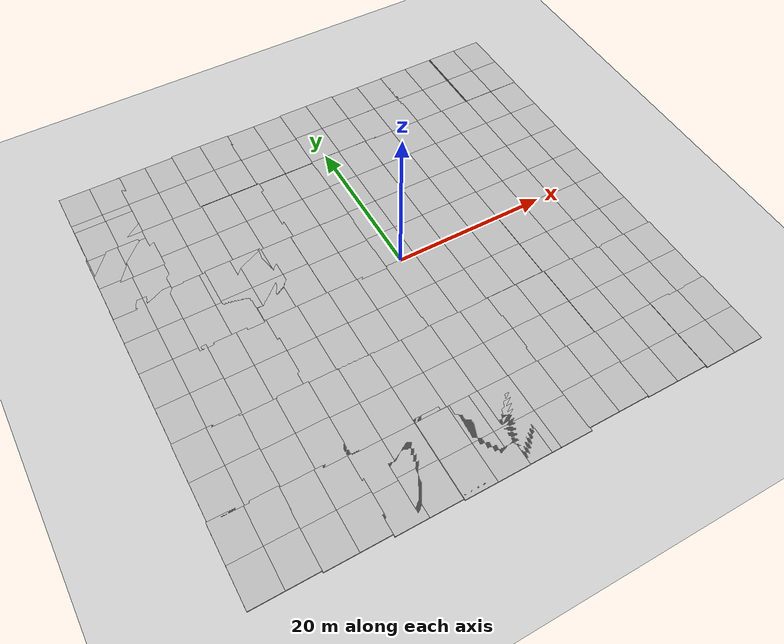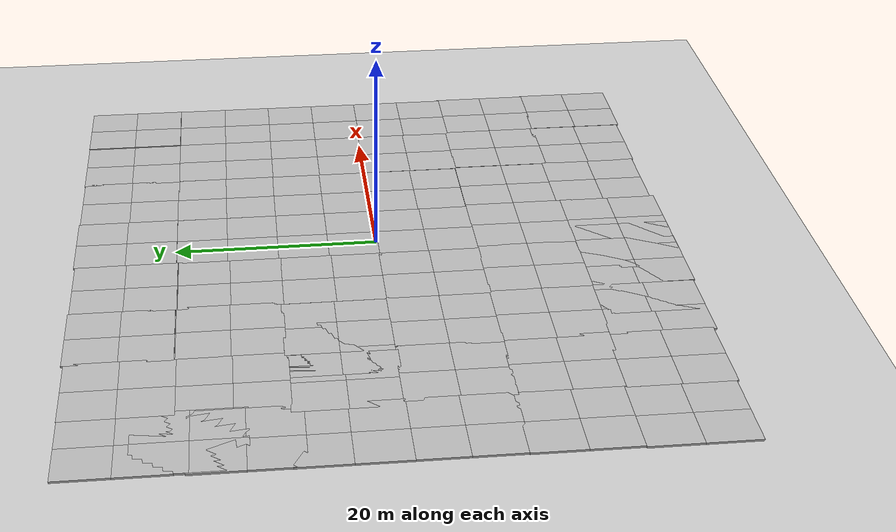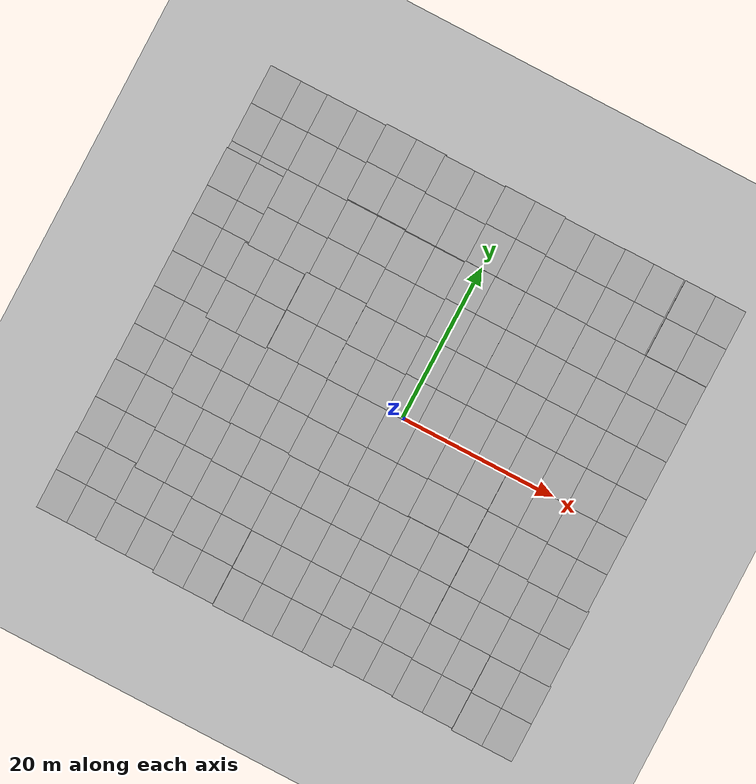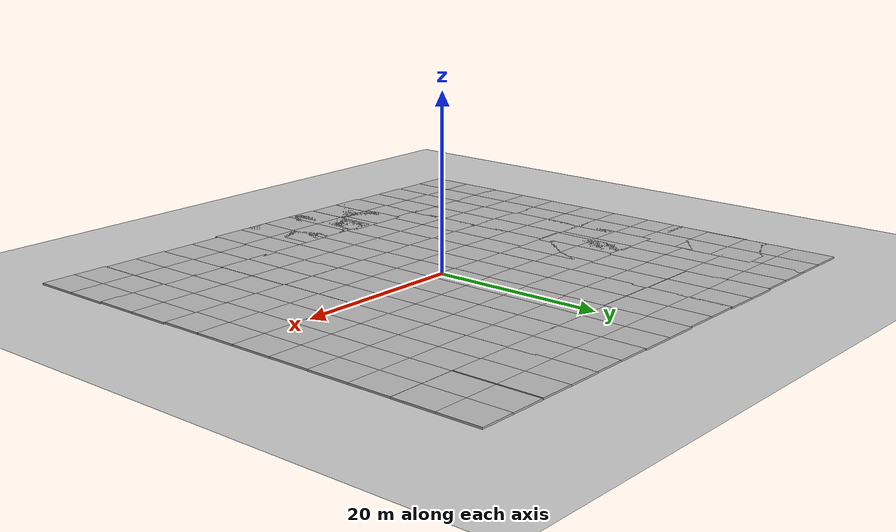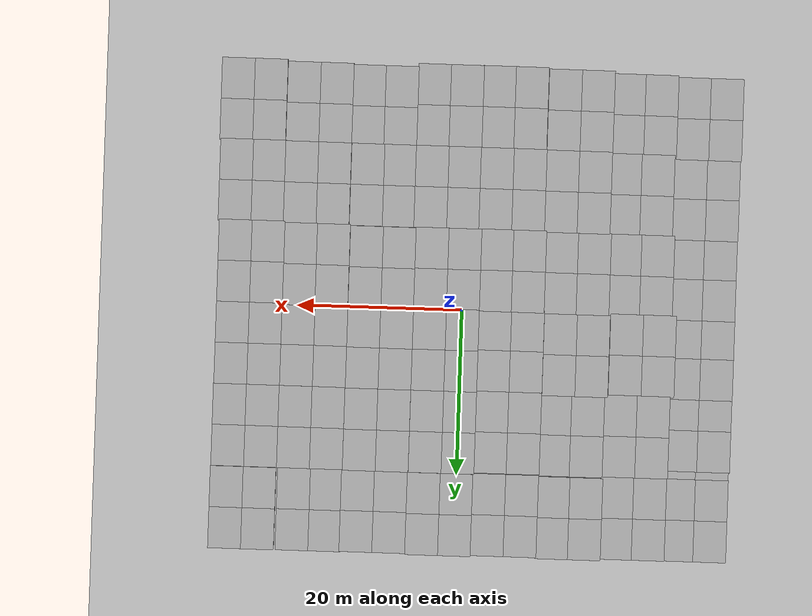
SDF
<sdf version="1.6">
 <world name="default">
  <light name="sun" type="directional">
   <pose>0 0 10 0 -0 0</pose>
   <diffuse>0.8 0.8 0.8 1</diffuse>
   <specular>0.1 0.1 0.1 1</specular>
   <attenuation>
    <range>1000</range>
    <constant>0.9</constant>
    <linear>0.01</linear>
    <quadratic>0.001</quadratic>
   </attenuation>
   <direction>-0.5 0.5 -1</direction>
  </light>
  <model name="ground_plane">
   <static>1</static>
   <link name="link">
    <collision name="collision">
     <geometry><plane><normal>0 0 1</normal><size>100 100</size></plane></geometry>
     <surface><friction><ode><mu>100</mu><mu2>50</mu2></ode></friction></surface>
    </collision>
    <visual name="visual">
     <cast_shadows>0</cast_shadows>
     <geometry><plane><normal>0 0 1</normal><size>100 100</size></plane></geometry>
     <material>
      <script><uri>file://media/materials/scripts/gazebo.material</uri><name>Gazebo/Grey</name></script>
     </material>
    </visual>
   </link>
  </model>
  <gravity>0 0 -9.8</gravity>
  <magnetic_field>6e-06 2.3e-05 -4.2e-05</magnetic_field>
  <atmosphere type="adiabatic"/>
  <physics name="default_physics" default="0" type="ode">
   <max_step_size>0.001</max_step_size>
   <real_time_factor>1</real_time_factor>
   <real_time_update_rate>1000</real_time_update_rate>
  </physics>
  <scene><ambient>0.4 0.4 0.4 1</ambient><background>0.7 0.7 0.7 1</background><shadows>1</shadows></scene>
  <spherical_coordinates>
   <surface_model>EARTH_WGS84</surface_model>
   <latitude_deg>0</latitude_deg>
   <longitude_deg>0</longitude_deg>
   <elevation>0</elevation>
   <heading_deg>0</heading_deg>
  </spherical_coordinates>
  <model name="mud_box">
   <static>1</static>
   <link name="link">
    <collision name="collision"><geometry><box><size>8 10 0.2</size></box></geometry></collision>
    <visual name="visual_1">
     <pose>-2 2.5 0 0 -0 0</pose>
     <cast_shadows>0</cast_shadows>
     <geometry><box><size>4 5 0.2</size></box></geometry>
     <material>
      <script>
       <uri>model://mud_box/materials/scripts</uri>
       <uri>model://mud_box/materials/textures</uri>
       <name>vrc/mud</name>
      </script>
     </material>
    </visual>
    <visual name="visual_2">
     <pose>2 2.5 0 0 -0 0</pose>
     <cast_shadows>0</cast_shadows>
     <geometry><box><size>4 5 0.2</size></box></geometry>
     <material>
      <script>
       <uri>model://mud_box/materials/scripts</uri>
       <uri>model://mud_box/materials/textures</uri>
       <name>vrc/mud</name>
      </script>
     </material>
    </visual>
    <visual name="visual_3">
     <pose>2 -2.5 0 0 -0 0</pose>
     <cast_shadows>0</cast_shadows>
     <geometry><box><size>4 5 0.2</size></box></geometry>
     <material>
      <script>
       <uri>model://mud_box/materials/scripts</uri>
       <uri>model://mud_box/materials/textures</uri>
       <name>vrc/mud</name>
      </script>
     </material>
    </visual>
    <visual name="visual_4">
     <pose>-2 -2.5 0 0 -0 0</pose>
     <cast_shadows>0</cast_shadows>
     <geometry><box><size>4 5 0.2</size></box></geometry>
     <material>
      <script>
       <uri>model://mud_box/materials/scripts</uri>
       <uri>model://mud_box/materials/textures</uri>
       <name>vrc/mud</name>
      </script>
     </material>
    </visual>
   </link>
   <pose>9.86832 14.8407 0 0 -0 0</pose>
  </model>
  <model name="mud_box_0">
   <static>1</static>
   <link name="link">
    <collision name="collision"><geometry><box><size>8 10 0.2</size></box></geometry></collision>
    <visual name="visual_1">
     <pose>-2 2.5 0 0 -0 0</pose>
     <cast_shadows>0</cast_shadows>
     <geometry><box><size>4 5 0.2</size></box></geometry>
     <material>
      <script>
       <uri>model://mud_box/materials/scripts</uri>
       <uri>model://mud_box/materials/textures</uri>
       <name>vrc/mud</name>
      </script>
     </material>
    </visual>
    <visual name="visual_2">
     <pose>2 2.5 0 0 -0 0</pose>
     <cast_shadows>0</cast_shadows>
     <geometry><box><size>4 5 0.2</size></box></geometry>
     <material>
      <script>
       <uri>model://mud_box/materials/scripts</uri>
       <uri>model://mud_box/materials/textures</uri>
       <name>vrc/mud</name>
      </script>
     </material>
    </visual>
    <visual name="visual_3">
     <pose>2 -2.5 0 0 -0 0</pose>
     <cast_shadows>0</cast_shadows>
     <geometry><box><size>4 5 0.2</size></box></geometry>
     <material>
      <script>
       <uri>model://mud_box/materials/scripts</uri>
       <uri>model://mud_box/materials/textures</uri>
       <name>vrc/mud</name>
      </script>
     </material>
    </visual>
    <visual name="visual_4">
     <pose>-2 -2.5 0 0 -0 0</pose>
     <cast_shadows>0</cast_shadows>
     <geometry><box><size>4 5 0.2</size></box></geometry>
     <material>
      <script>
       <uri>model://mud_box/materials/scripts</uri>
       <uri>model://mud_box/materials/textures</uri>
       <name>vrc/mud</name>
      </script>
     </material>
    </visual>
   </link>
   <pose>1.86767 4.83104 0 0 -0 0</pose>
  </model>
  <model name="mud_box_1">
   <static>1</static>
   <link name="link">
    <collision name="collision"><geometry><box><size>8 10 0.2</size></box></geometry></collision>
    <visual name="visual_1">
     <pose>-2 2.5 0 0 -0 0</pose>
     <cast_shadows>0</cast_shadows>
     <geometry><box><size>4 5 0.2</size></box></geometry>
     <material>
      <script>
       <uri>model://mud_box/materials/scripts</uri>
       <uri>model://mud_box/materials/textures</uri>
       <name>vrc/mud</name>
      </script>
     </material>
    </visual>
    <visual name="visual_2">
     <pose>2 2.5 0 0 -0 0</pose>
     <cast_shadows>0</cast_shadows>
     <geometry><box><size>4 5 0.2</size></box></geometry>
     <material>
      <script>
       <uri>model://mud_box/materials/scripts</uri>
       <uri>model://mud_box/materials/textures</uri>
       <name>vrc/mud</name>
      </script>
     </material>
    </visual>
    <visual name="visual_3">
     <pose>2 -2.5 0 0 -0 0</pose>
     <cast_shadows>0</cast_shadows>
     <geometry><box><size>4 5 0.2</size></box></geometry>
     <material>
      <script>
       <uri>model://mud_box/materials/scripts</uri>
       <uri>model://mud_box/materials/textures</uri>
       <name>vrc/mud</name>
      </script>
     </material>
    </visual>
    <visual name="visual_4">
     <pose>-2 -2.5 0 0 -0 0</pose>
     <cast_shadows>0</cast_shadows>
     <geometry><box><size>4 5 0.2</size></box></geometry>
     <material>
      <script>
       <uri>model://mud_box/materials/scripts</uri>
       <uri>model://mud_box/materials/textures</uri>
       <name>vrc/mud</name>
      </script>
     </material>
    </visual>
   </link>
   <pose>25.8304 -5.18145 0 0 -0 0</pose>
  </model>
  <model name="mud_box_2">
   <static>1</static>
   <link name="link">
    <collision name="collision"><geometry><box><size>8 10 0.2</size></box></geometry></collision>
    <visual name="visual_1">
     <pose>-2 2.5 0 0 -0 0</pose>
     <cast_shadows>0</cast_shadows>
     <geometry><box><size>4 5 0.2</size></box></geometry>
     <material>
      <script>
       <uri>model://mud_box/materials/scripts</uri>
       <uri>model://mud_box/materials/textures</uri>
       <name>vrc/mud</name>
      </script>
     </material>
    </visual>
    <visual name="visual_2">
     <pose>2 2.5 0 0 -0 0</pose>
     <cast_shadows>0</cast_shadows>
     <geometry><box><size>4 5 0.2</size></box></geometry>
     <material>
      <script>
       <uri>model://mud_box/materials/scripts</uri>
       <uri>model://mud_box/materials/textures</uri>
       <name>vrc/mud</name>
      </script>
     </material>
    </visual>
    <visual name="visual_3">
     <pose>2 -2.5 0 0 -0 0</pose>
     <cast_shadows>0</cast_shadows>
     <geometry><box><size>4 5 0.2</size></box></geometry>
     <material>
      <script>
       <uri>model://mud_box/materials/scripts</uri>
       <uri>model://mud_box/materials/textures</uri>
       <name>vrc/mud</name>
      </script>
     </material>
    </visual>
    <visual name="visual_4">
     <pose>-2 -2.5 0 0 -0 0</pose>
     <cast_shadows>0</cast_shadows>
     <geometry><box><size>4 5 0.2</size></box></geometry>
     <material>
      <script>
       <uri>model://mud_box/materials/scripts</uri>
       <uri>model://mud_box/materials/textures</uri>
       <name>vrc/mud</name>
      </script>
     </material>
    </visual>
   </link>
   <pose>1.88136 -5.00996 0 0 -0 0</pose>
  </model>
  <model name="mud_box_0_clone">
   <static>1</static>
   <link name="link">
    <collision name="collision"><geometry><box><size>8 10 0.2</size></box></geometry></collision>
    <visual name="visual_1">
     <pose>-2 2.5 0 0 -0 0</pose>
     <cast_shadows>0</cast_shadows>
     <geometry><box><size>4 5 0.2</size></box></geometry>
     <material>
      <script>
       <uri>model://mud_box/materials/scripts</uri>
       <uri>model://mud_box/materials/textures</uri>
       <name>vrc/mud</name>
      </script>
     </material>
    </visual>
    <visual name="visual_2">
     <pose>2 2.5 0 0 -0 0</pose>
     <cast_shadows>0</cast_shadows>
     <geometry><box><size>4 5 0.2</size></box></geometry>
     <material>
      <script>
       <uri>model://mud_box/materials/scripts</uri>
       <uri>model://mud_box/materials/textures</uri>
       <name>vrc/mud</name>
      </script>
     </material>
    </visual>
    <visual name="visual_3">
     <pose>2 -2.5 0 0 -0 0</pose>
     <cast_shadows>0</cast_shadows>
     <geometry><box><size>4 5 0.2</size></box></geometry>
     <material>
      <script>
       <uri>model://mud_box/materials/scripts</uri>
       <uri>model://mud_box/materials/textures</uri>
       <name>vrc/mud</name>
      </script>
     </material>
    </visual>
    <visual name="visual_4">
     <pose>-2 -2.5 0 0 -0 0</pose>
     <cast_shadows>0</cast_shadows>
     <geometry><box><size>4 5 0.2</size></box></geometry>
     <material>
      <script>
       <uri>model://mud_box/materials/scripts</uri>
       <uri>model://mud_box/materials/textures</uri>
       <name>vrc/mud</name>
      </script>
     </material>
    </visual>
   </link>
   <pose>9.84766 -4.91326 0 0 -0 0</pose>
  </model>
  <model name="mud_box_0_clone_clone">
   <static>1</static>
   <link name="link">
    <collision name="collision"><geometry><box><size>8 10 0.2</size></box></geometry></collision>
    <visual name="visual_1">
     <pose>-2 2.5 0 0 -0 0</pose>
     <cast_shadows>0</cast_shadows>
     <geometry><box><size>4 5 0.2</size></box></geometry>
     <material>
      <script>
       <uri>model://mud_box/materials/scripts</uri>
       <uri>model://mud_box/materials/textures</uri>
       <name>vrc/mud</name>
      </script>
     </material>
    </visual>
    <visual name="visual_2">
     <pose>2 2.5 0 0 -0 0</pose>
     <cast_shadows>0</cast_shadows>
     <geometry><box><size>4 5 0.2</size></box></geometry>
     <material>
      <script>
       <uri>model://mud_box/materials/scripts</uri>
       <uri>model://mud_box/materials/textures</uri>
       <name>vrc/mud</name>
      </script>
     </material>
    </visual>
    <visual name="visual_3">
     <pose>2 -2.5 0 0 -0 0</pose>
     <cast_shadows>0</cast_shadows>
     <geometry><box><size>4 5 0.2</size></box></geometry>
     <material>
      <script>
       <uri>model://mud_box/materials/scripts</uri>
       <uri>model://mud_box/materials/textures</uri>
       <name>vrc/mud</name>
      </script>
     </material>
    </visual>
    <visual name="visual_4">
     <pose>-2 -2.5 0 0 -0 0</pose>
     <cast_shadows>0</cast_shadows>
     <geometry><box><size>4 5 0.2</size></box></geometry>
     <material>
      <script>
       <uri>model://mud_box/materials/scripts</uri>
       <uri>model://mud_box/materials/textures</uri>
       <name>vrc/mud</name>
      </script>
     </material>
    </visual>
   </link>
   <pose>17.874 -5.03497 0 0 -0 0</pose>
  </model>
  <model name="mud_box_0_clone_clone_0">
   <static>1</static>
   <link name="link">
    <collision name="collision"><geometry><box><size>8 10 0.2</size></box></geometry></collision>
    <visual name="visual_1">
     <pose>-2 2.5 0 0 -0 0</pose>
     <cast_shadows>0</cast_shadows>
     <geometry><box><size>4 5 0.2</size></box></geometry>
     <material>
      <script>
       <uri>model://mud_box/materials/scripts</uri>
       <uri>model://mud_box/materials/textures</uri>
       <name>vrc/mud</name>
      </script>
     </material>
    </visual>
    <visual name="visual_2">
     <pose>2 2.5 0 0 -0 0</pose>
     <cast_shadows>0</cast_shadows>
     <geometry><box><size>4 5 0.2</size></box></geometry>
     <material>
      <script>
       <uri>model://mud_box/materials/scripts</uri>
       <uri>model://mud_box/materials/textures</uri>
       <name>vrc/mud</name>
      </script>
     </material>
    </visual>
    <visual name="visual_3">
     <pose>2 -2.5 0 0 -0 0</pose>
     <cast_shadows>0</cast_shadows>
     <geometry><box><size>4 5 0.2</size></box></geometry>
     <material>
      <script>
       <uri>model://mud_box/materials/scripts</uri>
       <uri>model://mud_box/materials/textures</uri>
       <name>vrc/mud</name>
      </script>
     </material>
    </visual>
    <visual name="visual_4">
     <pose>-2 -2.5 0 0 -0 0</pose>
     <cast_shadows>0</cast_shadows>
     <geometry><box><size>4 5 0.2</size></box></geometry>
     <material>
      <script>
       <uri>model://mud_box/materials/scripts</uri>
       <uri>model://mud_box/materials/textures</uri>
       <name>vrc/mud</name>
      </script>
     </material>
    </visual>
   </link>
   <pose>17.8432 4.79546 0 0 -0 0</pose>
  </model>
  <model name="mud_box_0_clone_clone_1">
   <static>1</static>
   <link name="link">
    <collision name="collision"><geometry><box><size>8 10 0.2</size></box></geometry></collision>
    <visual name="visual_1">
     <pose>-2 2.5 0 0 -0 0</pose>
     <cast_shadows>0</cast_shadows>
     <geometry><box><size>4 5 0.2</size></box></geometry>
     <material>
      <script>
       <uri>model://mud_box/materials/scripts</uri>
       <uri>model://mud_box/materials/textures</uri>
       <name>vrc/mud</name>
      </script>
     </material>
    </visual>
    <visual name="visual_2">
     <pose>2 2.5 0 0 -0 0</pose>
     <cast_shadows>0</cast_shadows>
     <geometry><box><size>4 5 0.2</size></box></geometry>
     <material>
      <script>
       <uri>model://mud_box/materials/scripts</uri>
       <uri>model://mud_box/materials/textures</uri>
       <name>vrc/mud</name>
      </script>
     </material>
    </visual>
    <visual name="visual_3">
     <pose>2 -2.5 0 0 -0 0</pose>
     <cast_shadows>0</cast_shadows>
     <geometry><box><size>4 5 0.2</size></box></geometry>
     <material>
      <script>
       <uri>model://mud_box/materials/scripts</uri>
       <uri>model://mud_box/materials/textures</uri>
       <name>vrc/mud</name>
      </script>
     </material>
    </visual>
    <visual name="visual_4">
     <pose>-2 -2.5 0 0 -0 0</pose>
     <cast_shadows>0</cast_shadows>
     <geometry><box><size>4 5 0.2</size></box></geometry>
     <material>
      <script>
       <uri>model://mud_box/materials/scripts</uri>
       <uri>model://mud_box/materials/textures</uri>
       <name>vrc/mud</name>
      </script>
     </material>
    </visual>
   </link>
   <pose>25.8322 4.79818 0 0 -0 0</pose>
  </model>
  <model name="mud_box_0_clone_clone_2">
   <static>1</static>
   <link name="link">
    <collision name="collision"><geometry><box><size>8 10 0.2</size></box></geometry></collision>
    <visual name="visual_1">
     <pose>-2 2.5 0 0 -0 0</pose>
     <cast_shadows>0</cast_shadows>
     <geometry><box><size>4 5 0.2</size></box></geometry>
     <material>
      <script>
       <uri>model://mud_box/materials/scripts</uri>
       <uri>model://mud_box/materials/textures</uri>
       <name>vrc/mud</name>
      </script>
     </material>
    </visual>
    <visual name="visual_2">
     <pose>2 2.5 0 0 -0 0</pose>
     <cast_shadows>0</cast_shadows>
     <geometry><box><size>4 5 0.2</size></box></geometry>
     <material>
      <script>
       <uri>model://mud_box/materials/scripts</uri>
       <uri>model://mud_box/materials/textures</uri>
       <name>vrc/mud</name>
      </script>
     </material>
    </visual>
    <visual name="visual_3">
     <pose>2 -2.5 0 0 -0 0</pose>
     <cast_shadows>0</cast_shadows>
     <geometry><box><size>4 5 0.2</size></box></geometry>
     <material>
      <script>
       <uri>model://mud_box/materials/scripts</uri>
       <uri>model://mud_box/materials/textures</uri>
       <name>vrc/mud</name>
      </script>
     </material>
    </visual>
    <visual name="visual_4">
     <pose>-2 -2.5 0 0 -0 0</pose>
     <cast_shadows>0</cast_shadows>
     <geometry><box><size>4 5 0.2</size></box></geometry>
     <material>
      <script>
       <uri>model://mud_box/materials/scripts</uri>
       <uri>model://mud_box/materials/textures</uri>
       <name>vrc/mud</name>
      </script>
     </material>
    </visual>
   </link>
   <pose>1.86503 14.8262 0 0 -0 0</pose>
  </model>
  <model name="mud_box_4">
   <static>1</static>
   <link name="link">
    <collision name="collision"><geometry><box><size>8 10 0.2</size></box></geometry></collision>
    <visual name="visual_1">
     <pose>-2 2.5 0 0 -0 0</pose>
     <cast_shadows>0</cast_shadows>
     <geometry><box><size>4 5 0.2</size></box></geometry>
     <material>
      <script>
       <uri>model://mud_box/materials/scripts</uri>
       <uri>model://mud_box/materials/textures</uri>
       <name>vrc/mud</name>
      </script>
     </material>
    </visual>
    <visual name="visual_2">
     <pose>2 2.5 0 0 -0 0</pose>
     <cast_shadows>0</cast_shadows>
     <geometry><box><size>4 5 0.2</size></box></geometry>
     <material>
      <script>
       <uri>model://mud_box/materials/scripts</uri>
       <uri>model://mud_box/materials/textures</uri>
       <name>vrc/mud</name>
      </script>
     </material>
    </visual>
    <visual name="visual_3">
     <pose>2 -2.5 0 0 -0 0</pose>
     <cast_shadows>0</cast_shadows>
     <geometry><box><size>4 5 0.2</size></box></geometry>
     <material>
      <script>
       <uri>model://mud_box/materials/scripts</uri>
       <uri>model://mud_box/materials/textures</uri>
       <name>vrc/mud</name>
      </script>
     </material>
    </visual>
    <visual name="visual_4">
     <pose>-2 -2.5 0 0 -0 0</pose>
     <cast_shadows>0</cast_shadows>
     <geometry><box><size>4 5 0.2</size></box></geometry>
     <material>
      <script>
       <uri>model://mud_box/materials/scripts</uri>
       <uri>model://mud_box/materials/textures</uri>
       <name>vrc/mud</name>
      </script>
     </material>
    </visual>
   </link>
   <pose>9.86465 4.85433 0 0 -0 0</pose>
  </model>
  <model name="mud_box_3">
   <static>1</static>
   <link name="link">
    <collision name="collision"><geometry><box><size>8 10 0.2</size></box></geometry></collision>
    <visual name="visual_1">
     <pose>-2 2.5 0 0 -0 0</pose>
     <cast_shadows>0</cast_shadows>
     <geometry><box><size>4 5 0.2</size></box></geometry>
     <material>
      <script>
       <uri>model://mud_box/materials/scripts</uri>
       <uri>model://mud_box/materials/textures</uri>
       <name>vrc/mud</name>
      </script>
     </material>
    </visual>
    <visual name="visual_2">
     <pose>2 2.5 0 0 -0 0</pose>
     <cast_shadows>0</cast_shadows>
     <geometry><box><size>4 5 0.2</size></box></geometry>
     <material>
      <script>
       <uri>model://mud_box/materials/scripts</uri>
       <uri>model://mud_box/materials/textures</uri>
       <name>vrc/mud</name>
      </script>
     </material>
    </visual>
    <visual name="visual_3">
     <pose>2 -2.5 0 0 -0 0</pose>
     <cast_shadows>0</cast_shadows>
     <geometry><box><size>4 5 0.2</size></box></geometry>
     <material>
      <script>
       <uri>model://mud_box/materials/scripts</uri>
       <uri>model://mud_box/materials/textures</uri>
       <name>vrc/mud</name>
      </script>
     </material>
    </visual>
    <visual name="visual_4">
     <pose>-2 -2.5 0 0 -0 0</pose>
     <cast_shadows>0</cast_shadows>
     <geometry><box><size>4 5 0.2</size></box></geometry>
     <material>
      <script>
       <uri>model://mud_box/materials/scripts</uri>
       <uri>model://mud_box/materials/textures</uri>
       <name>vrc/mud</name>
      </script>
     </material>
    </visual>
   </link>
   <pose>17.8698 14.7961 0 0 -0 0</pose>
  </model>
  <model name="mud_box_5">
   <static>1</static>
   <link name="link">
    <collision name="collision"><geometry><box><size>8 10 0.2</size></box></geometry></collision>
    <visual name="visual_1">
     <pose>-2 2.5 0 0 -0 0</pose>
     <cast_shadows>0</cast_shadows>
     <geometry><box><size>4 5 0.2</size></box></geometry>
     <material>
      <script>
       <uri>model://mud_box/materials/scripts</uri>
       <uri>model://mud_box/materials/textures</uri>
       <name>vrc/mud</name>
      </script>
     </material>
    </visual>
    <visual name="visual_2">
     <pose>2 2.5 0 0 -0 0</pose>
     <cast_shadows>0</cast_shadows>
     <geometry><box><size>4 5 0.2</size></box></geometry>
     <material>
      <script>
       <uri>model://mud_box/materials/scripts</uri>
       <uri>model://mud_box/materials/textures</uri>
       <name>vrc/mud</name>
      </script>
     </material>
    </visual>
    <visual name="visual_3">
     <pose>2 -2.5 0 0 -0 0</pose>
     <cast_shadows>0</cast_shadows>
     <geometry><box><size>4 5 0.2</size></box></geometry>
     <material>
      <script>
       <uri>model://mud_box/materials/scripts</uri>
       <uri>model://mud_box/materials/textures</uri>
       <name>vrc/mud</name>
      </script>
     </material>
    </visual>
    <visual name="visual_4">
     <pose>-2 -2.5 0 0 -0 0</pose>
     <cast_shadows>0</cast_shadows>
     <geometry><box><size>4 5 0.2</size></box></geometry>
     <material>
      <script>
       <uri>model://mud_box/materials/scripts</uri>
       <uri>model://mud_box/materials/textures</uri>
       <name>vrc/mud</name>
      </script>
     </material>
    </visual>
   </link>
   <pose>25.863 14.7854 0 0 -0 0</pose>
  </model>
  <model name="mud_box_2_clone">
   <static>1</static>
   <link name="link">
    <collision name="collision"><geometry><box><size>8 10 0.2</size></box></geometry></collision>
    <visual name="visual_1">
     <pose>-2 2.5 0 0 -0 0</pose>
     <cast_shadows>0</cast_shadows>
     <geometry><box><size>4 5 0.2</size></box></geometry>
     <material>
      <script>
       <uri>model://mud_box/materials/scripts</uri>
       <uri>model://mud_box/materials/textures</uri>
       <name>vrc/mud</name>
      </script>
     </material>
    </visual>
    <visual name="visual_2">
     <pose>2 2.5 0 0 -0 0</pose>
     <cast_shadows>0</cast_shadows>
     <geometry><box><size>4 5 0.2</size></box></geometry>
     <material>
      <script>
       <uri>model://mud_box/materials/scripts</uri>
       <uri>model://mud_box/materials/textures</uri>
       <name>vrc/mud</name>
      </script>
     </material>
    </visual>
    <visual name="visual_3">
     <pose>2 -2.5 0 0 -0 0</pose>
     <cast_shadows>0</cast_shadows>
     <geometry><box><size>4 5 0.2</size></box></geometry>
     <material>
      <script>
       <uri>model://mud_box/materials/scripts</uri>
       <uri>model://mud_box/materials/textures</uri>
       <name>vrc/mud</name>
      </script>
     </material>
    </visual>
    <visual name="visual_4">
     <pose>-2 -2.5 0 0 -0 0</pose>
     <cast_shadows>0</cast_shadows>
     <geometry><box><size>4 5 0.2</size></box></geometry>
     <material>
      <script>
       <uri>model://mud_box/materials/scripts</uri>
       <uri>model://mud_box/materials/textures</uri>
       <name>vrc/mud</name>
      </script>
     </material>
    </visual>
   </link>
   <pose>-5.99711 -5.05363 0 0 -0 0</pose>
  </model>
  <model name="mud_box_2_clone_0">
   <static>1</static>
   <link name="link">
    <collision name="collision"><geometry><box><size>8 10 0.2</size></box></geometry></collision>
    <visual name="visual_1">
     <pose>-2 2.5 0 0 -0 0</pose>
     <cast_shadows>0</cast_shadows>
     <geometry><box><size>4 5 0.2</size></box></geometry>
     <material>
      <script>
       <uri>model://mud_box/materials/scripts</uri>
       <uri>model://mud_box/materials/textures</uri>
       <name>vrc/mud</name>
      </script>
     </material>
    </visual>
    <visual name="visual_2">
     <pose>2 2.5 0 0 -0 0</pose>
     <cast_shadows>0</cast_shadows>
     <geometry><box><size>4 5 0.2</size></box></geometry>
     <material>
      <script>
       <uri>model://mud_box/materials/scripts</uri>
       <uri>model://mud_box/materials/textures</uri>
       <name>vrc/mud</name>
      </script>
     </material>
    </visual>
    <visual name="visual_3">
     <pose>2 -2.5 0 0 -0 0</pose>
     <cast_shadows>0</cast_shadows>
     <geometry><box><size>4 5 0.2</size></box></geometry>
     <material>
      <script>
       <uri>model://mud_box/materials/scripts</uri>
       <uri>model://mud_box/materials/textures</uri>
       <name>vrc/mud</name>
      </script>
     </material>
    </visual>
    <visual name="visual_4">
     <pose>-2 -2.5 0 0 -0 0</pose>
     <cast_shadows>0</cast_shadows>
     <geometry><box><size>4 5 0.2</size></box></geometry>
     <material>
      <script>
       <uri>model://mud_box/materials/scripts</uri>
       <uri>model://mud_box/materials/textures</uri>
       <name>vrc/mud</name>
      </script>
     </material>
    </visual>
   </link>
   <pose>-6.06019 4.66559 0 0 -0 0</pose>
  </model>
  <model name="mud_box_2_clone_1">
   <static>1</static>
   <link name="link">
    <collision name="collision"><geometry><box><size>8 10 0.2</size></box></geometry></collision>
    <visual name="visual_1">
     <pose>-2 2.5 0 0 -0 0</pose>
     <cast_shadows>0</cast_shadows>
     <geometry><box><size>4 5 0.2</size></box></geometry>
     <material>
      <script>
       <uri>model://mud_box/materials/scripts</uri>
       <uri>model://mud_box/materials/textures</uri>
       <name>vrc/mud</name>
      </script>
     </material>
    </visual>
    <visual name="visual_2">
     <pose>2 2.5 0 0 -0 0</pose>
     <cast_shadows>0</cast_shadows>
     <geometry><box><size>4 5 0.2</size></box></geometry>
     <material>
      <script>
       <uri>model://mud_box/materials/scripts</uri>
       <uri>model://mud_box/materials/textures</uri>
       <name>vrc/mud</name>
      </script>
     </material>
    </visual>
    <visual name="visual_3">
     <pose>2 -2.5 0 0 -0 0</pose>
     <cast_shadows>0</cast_shadows>
     <geometry><box><size>4 5 0.2</size></box></geometry>
     <material>
      <script>
       <uri>model://mud_box/materials/scripts</uri>
       <uri>model://mud_box/materials/textures</uri>
       <name>vrc/mud</name>
      </script>
     </material>
    </visual>
    <visual name="visual_4">
     <pose>-2 -2.5 0 0 -0 0</pose>
     <cast_shadows>0</cast_shadows>
     <geometry><box><size>4 5 0.2</size></box></geometry>
     <material>
      <script>
       <uri>model://mud_box/materials/scripts</uri>
       <uri>model://mud_box/materials/textures</uri>
       <name>vrc/mud</name>
      </script>
     </material>
    </visual>
   </link>
   <pose>-6.05112 14.6239 0 0 -0 0</pose>
  </model>
  <model name="mud_box_2_clone_2">
   <static>1</static>
   <link name="link">
    <collision name="collision"><geometry><box><size>8 10 0.2</size></box></geometry></collision>
    <visual name="visual_1">
     <pose>-2 2.5 0 0 -0 0</pose>
     <cast_shadows>0</cast_shadows>
     <geometry><box><size>4 5 0.2</size></box></geometry>
     <material>
      <script>
       <uri>model://mud_box/materials/scripts</uri>
       <uri>model://mud_box/materials/textures</uri>
       <name>vrc/mud</name>
      </script>
     </material>
    </visual>
    <visual name="visual_2">
     <pose>2 2.5 0 0 -0 0</pose>
     <cast_shadows>0</cast_shadows>
     <geometry><box><size>4 5 0.2</size></box></geometry>
     <material>
      <script>
       <uri>model://mud_box/materials/scripts</uri>
       <uri>model://mud_box/materials/textures</uri>
       <name>vrc/mud</name>
      </script>
     </material>
    </visual>
    <visual name="visual_3">
     <pose>2 -2.5 0 0 -0 0</pose>
     <cast_shadows>0</cast_shadows>
     <geometry><box><size>4 5 0.2</size></box></geometry>
     <material>
      <script>
       <uri>model://mud_box/materials/scripts</uri>
       <uri>model://mud_box/materials/textures</uri>
       <name>vrc/mud</name>
      </script>
     </material>
    </visual>
    <visual name="visual_4">
     <pose>-2 -2.5 0 0 -0 0</pose>
     <cast_shadows>0</cast_shadows>
     <geometry><box><size>4 5 0.2</size></box></geometry>
     <material>
      <script>
       <uri>model://mud_box/materials/scripts</uri>
       <uri>model://mud_box/materials/textures</uri>
       <name>vrc/mud</name>
      </script>
     </material>
    </visual>
   </link>
   <pose>-6.01342 24.6918 0 0 -0 0</pose>
  </model>
  <model name="mud_box_2_clone_3">
   <static>1</static>
   <link name="link">
    <collision name="collision"><geometry><box><size>8 10 0.2</size></box></geometry></collision>
    <visual name="visual_1">
     <pose>-2 2.5 0 0 -0 0</pose>
     <cast_shadows>0</cast_shadows>
     <geometry><box><size>4 5 0.2</size></box></geometry>
     <material>
      <script>
       <uri>model://mud_box/materials/scripts</uri>
       <uri>model://mud_box/materials/textures</uri>
       <name>vrc/mud</name>
      </script>
     </material>
    </visual>
    <visual name="visual_2">
     <pose>2 2.5 0 0 -0 0</pose>
     <cast_shadows>0</cast_shadows>
     <geometry><box><size>4 5 0.2</size></box></geometry>
     <material>
      <script>
       <uri>model://mud_box/materials/scripts</uri>
       <uri>model://mud_box/materials/textures</uri>
       <name>vrc/mud</name>
      </script>
     </material>
    </visual>
    <visual name="visual_3">
     <pose>2 -2.5 0 0 -0 0</pose>
     <cast_shadows>0</cast_shadows>
     <geometry><box><size>4 5 0.2</size></box></geometry>
     <material>
      <script>
       <uri>model://mud_box/materials/scripts</uri>
       <uri>model://mud_box/materials/textures</uri>
       <name>vrc/mud</name>
      </script>
     </material>
    </visual>
    <visual name="visual_4">
     <pose>-2 -2.5 0 0 -0 0</pose>
     <cast_shadows>0</cast_shadows>
     <geometry><box><size>4 5 0.2</size></box></geometry>
     <material>
      <script>
       <uri>model://mud_box/materials/scripts</uri>
       <uri>model://mud_box/materials/textures</uri>
       <name>vrc/mud</name>
      </script>
     </material>
    </visual>
   </link>
   <pose>1.9474 24.8331 0 0 -0 0</pose>
  </model>
  <model name="mud_box_2_clone_4">
   <static>1</static>
   <link name="link">
    <collision name="collision"><geometry><box><size>8 10 0.2</size></box></geometry></collision>
    <visual name="visual_1">
     <pose>-2 2.5 0 0 -0 0</pose>
     <cast_shadows>0</cast_shadows>
     <geometry><box><size>4 5 0.2</size></box></geometry>
     <material>
      <script>
       <uri>model://mud_box/materials/scripts</uri>
       <uri>model://mud_box/materials/textures</uri>
       <name>vrc/mud</name>
      </script>
     </material>
    </visual>
    <visual name="visual_2">
     <pose>2 2.5 0 0 -0 0</pose>
     <cast_shadows>0</cast_shadows>
     <geometry><box><size>4 5 0.2</size></box></geometry>
     <material>
      <script>
       <uri>model://mud_box/materials/scripts</uri>
       <uri>model://mud_box/materials/textures</uri>
       <name>vrc/mud</name>
      </script>
     </material>
    </visual>
    <visual name="visual_3">
     <pose>2 -2.5 0 0 -0 0</pose>
     <cast_shadows>0</cast_shadows>
     <geometry><box><size>4 5 0.2</size></box></geometry>
     <material>
      <script>
       <uri>model://mud_box/materials/scripts</uri>
       <uri>model://mud_box/materials/textures</uri>
       <name>vrc/mud</name>
      </script>
     </material>
    </visual>
    <visual name="visual_4">
     <pose>-2 -2.5 0 0 -0 0</pose>
     <cast_shadows>0</cast_shadows>
     <geometry><box><size>4 5 0.2</size></box></geometry>
     <material>
      <script>
       <uri>model://mud_box/materials/scripts</uri>
       <uri>model://mud_box/materials/textures</uri>
       <name>vrc/mud</name>
      </script>
     </material>
    </visual>
   </link>
   <pose>9.9456 24.7245 0 0 -0 0</pose>
  </model>
  <model name="mud_box_2_clone_5">
   <static>1</static>
   <link name="link">
    <collision name="collision"><geometry><box><size>8 10 0.2</size></box></geometry></collision>
    <visual name="visual_1">
     <pose>-2 2.5 0 0 -0 0</pose>
     <cast_shadows>0</cast_shadows>
     <geometry><box><size>4 5 0.2</size></box></geometry>
     <material>
      <script>
       <uri>model://mud_box/materials/scripts</uri>
       <uri>model://mud_box/materials/textures</uri>
       <name>vrc/mud</name>
      </script>
     </material>
    </visual>
    <visual name="visual_2">
     <pose>2 2.5 0 0 -0 0</pose>
     <cast_shadows>0</cast_shadows>
     <geometry><box><size>4 5 0.2</size></box></geometry>
     <material>
      <script>
       <uri>model://mud_box/materials/scripts</uri>
       <uri>model://mud_box/materials/textures</uri>
       <name>vrc/mud</name>
      </script>
     </material>
    </visual>
    <visual name="visual_3">
     <pose>2 -2.5 0 0 -0 0</pose>
     <cast_shadows>0</cast_shadows>
     <geometry><box><size>4 5 0.2</size></box></geometry>
     <material>
      <script>
       <uri>model://mud_box/materials/scripts</uri>
       <uri>model://mud_box/materials/textures</uri>
       <name>vrc/mud</name>
      </script>
     </material>
    </visual>
    <visual name="visual_4">
     <pose>-2 -2.5 0 0 -0 0</pose>
     <cast_shadows>0</cast_shadows>
     <geometry><box><size>4 5 0.2</size></box></geometry>
     <material>
      <script>
       <uri>model://mud_box/materials/scripts</uri>
       <uri>model://mud_box/materials/textures</uri>
       <name>vrc/mud</name>
      </script>
     </material>
    </visual>
   </link>
   <pose>17.7255 24.7838 0 0 -0 0</pose>
  </model>
  <model name="mud_box_2_clone_6">
   <static>1</static>
   <link name="link">
    <collision name="collision"><geometry><box><size>8 10 0.2</size></box></geometry></collision>
    <visual name="visual_1">
     <pose>-2 2.5 0 0 -0 0</pose>
     <cast_shadows>0</cast_shadows>
     <geometry><box><size>4 5 0.2</size></box></geometry>
     <material>
      <script>
       <uri>model://mud_box/materials/scripts</uri>
       <uri>model://mud_box/materials/textures</uri>
       <name>vrc/mud</name>
      </script>
     </material>
    </visual>
    <visual name="visual_2">
     <pose>2 2.5 0 0 -0 0</pose>
     <cast_shadows>0</cast_shadows>
     <geometry><box><size>4 5 0.2</size></box></geometry>
     <material>
      <script>
       <uri>model://mud_box/materials/scripts</uri>
       <uri>model://mud_box/materials/textures</uri>
       <name>vrc/mud</name>
      </script>
     </material>
    </visual>
    <visual name="visual_3">
     <pose>2 -2.5 0 0 -0 0</pose>
     <cast_shadows>0</cast_shadows>
     <geometry><box><size>4 5 0.2</size></box></geometry>
     <material>
      <script>
       <uri>model://mud_box/materials/scripts</uri>
       <uri>model://mud_box/materials/textures</uri>
       <name>vrc/mud</name>
      </script>
     </material>
    </visual>
    <visual name="visual_4">
     <pose>-2 -2.5 0 0 -0 0</pose>
     <cast_shadows>0</cast_shadows>
     <geometry><box><size>4 5 0.2</size></box></geometry>
     <material>
      <script>
       <uri>model://mud_box/materials/scripts</uri>
       <uri>model://mud_box/materials/textures</uri>
       <name>vrc/mud</name>
      </script>
     </material>
    </visual>
   </link>
   <pose>25.9029 24.817 0 0 -0 0</pose>
  </model>
  <model name="mud_box_2_clone_7">
   <static>1</static>
   <link name="link">
    <collision name="collision"><geometry><box><size>8 10 0.2</size></box></geometry></collision>
    <visual name="visual_1">
     <pose>-2 2.5 0 0 -0 0</pose>
     <cast_shadows>0</cast_shadows>
     <geometry><box><size>4 5 0.2</size></box></geometry>
     <material>
      <script>
       <uri>model://mud_box/materials/scripts</uri>
       <uri>model://mud_box/materials/textures</uri>
       <name>vrc/mud</name>
      </script>
     </material>
    </visual>
    <visual name="visual_2">
     <pose>2 2.5 0 0 -0 0</pose>
     <cast_shadows>0</cast_shadows>
     <geometry><box><size>4 5 0.2</size></box></geometry>
     <material>
      <script>
       <uri>model://mud_box/materials/scripts</uri>
       <uri>model://mud_box/materials/textures</uri>
       <name>vrc/mud</name>
      </script>
     </material>
    </visual>
    <visual name="visual_3">
     <pose>2 -2.5 0 0 -0 0</pose>
     <cast_shadows>0</cast_shadows>
     <geometry><box><size>4 5 0.2</size></box></geometry>
     <material>
      <script>
       <uri>model://mud_box/materials/scripts</uri>
       <uri>model://mud_box/materials/textures</uri>
       <name>vrc/mud</name>
      </script>
     </material>
    </visual>
    <visual name="visual_4">
     <pose>-2 -2.5 0 0 -0 0</pose>
     <cast_shadows>0</cast_shadows>
     <geometry><box><size>4 5 0.2</size></box></geometry>
     <material>
      <script>
       <uri>model://mud_box/materials/scripts</uri>
       <uri>model://mud_box/materials/textures</uri>
       <name>vrc/mud</name>
      </script>
     </material>
    </visual>
   </link>
   <pose>-5.71358 -14.9574 0 0 -0 0</pose>
  </model>
  <model name="mud_box_2_clone_8">
   <static>1</static>
   <link name="link">
    <collision name="collision"><geometry><box><size>8 10 0.2</size></box></geometry></collision>
    <visual name="visual_1">
     <pose>-2 2.5 0 0 -0 0</pose>
     <cast_shadows>0</cast_shadows>
     <geometry><box><size>4 5 0.2</size></box></geometry>
     <material>
      <script>
       <uri>model://mud_box/materials/scripts</uri>
       <uri>model://mud_box/materials/textures</uri>
       <name>vrc/mud</name>
      </script>
     </material>
    </visual>
    <visual name="visual_2">
     <pose>2 2.5 0 0 -0 0</pose>
     <cast_shadows>0</cast_shadows>
     <geometry><box><size>4 5 0.2</size></box></geometry>
     <material>
      <script>
       <uri>model://mud_box/materials/scripts</uri>
       <uri>model://mud_box/materials/textures</uri>
       <name>vrc/mud</name>
      </script>
     </material>
    </visual>
    <visual name="visual_3">
     <pose>2 -2.5 0 0 -0 0</pose>
     <cast_shadows>0</cast_shadows>
     <geometry><box><size>4 5 0.2</size></box></geometry>
     <material>
      <script>
       <uri>model://mud_box/materials/scripts</uri>
       <uri>model://mud_box/materials/textures</uri>
       <name>vrc/mud</name>
      </script>
     </material>
    </visual>
    <visual name="visual_4">
     <pose>-2 -2.5 0 0 -0 0</pose>
     <cast_shadows>0</cast_shadows>
     <geometry><box><size>4 5 0.2</size></box></geometry>
     <material>
      <script>
       <uri>model://mud_box/materials/scripts</uri>
       <uri>model://mud_box/materials/textures</uri>
       <name>vrc/mud</name>
      </script>
     </material>
    </visual>
   </link>
   <pose>2.1899 -14.9558 0 0 -0 0</pose>
  </model>
  <model name="mud_box_2_clone_9">
   <static>1</static>
   <link name="link">
    <collision name="collision"><geometry><box><size>8 10 0.2</size></box></geometry></collision>
    <visual name="visual_1">
     <pose>-2 2.5 0 0 -0 0</pose>
     <cast_shadows>0</cast_shadows>
     <geometry><box><size>4 5 0.2</size></box></geometry>
     <material>
      <script>
       <uri>model://mud_box/materials/scripts</uri>
       <uri>model://mud_box/materials/textures</uri>
       <name>vrc/mud</name>
      </script>
     </material>
    </visual>
    <visual name="visual_2">
     <pose>2 2.5 0 0 -0 0</pose>
     <cast_shadows>0</cast_shadows>
     <geometry><box><size>4 5 0.2</size></box></geometry>
     <material>
      <script>
       <uri>model://mud_box/materials/scripts</uri>
       <uri>model://mud_box/materials/textures</uri>
       <name>vrc/mud</name>
      </script>
     </material>
    </visual>
    <visual name="visual_3">
     <pose>2 -2.5 0 0 -0 0</pose>
     <cast_shadows>0</cast_shadows>
     <geometry><box><size>4 5 0.2</size></box></geometry>
     <material>
      <script>
       <uri>model://mud_box/materials/scripts</uri>
       <uri>model://mud_box/materials/textures</uri>
       <name>vrc/mud</name>
      </script>
     </material>
    </visual>
    <visual name="visual_4">
     <pose>-2 -2.5 0 0 -0 0</pose>
     <cast_shadows>0</cast_shadows>
     <geometry><box><size>4 5 0.2</size></box></geometry>
     <material>
      <script>
       <uri>model://mud_box/materials/scripts</uri>
       <uri>model://mud_box/materials/textures</uri>
       <name>vrc/mud</name>
      </script>
     </material>
    </visual>
   </link>
   <pose>10.0209 -14.9415 0 0 -0 0</pose>
  </model>
  <model name="mud_box_2_clone_10">
   <static>1</static>
   <link name="link">
    <collision name="collision"><geometry><box><size>8 10 0.2</size></box></geometry></collision>
    <visual name="visual_1">
     <pose>-2 2.5 0 0 -0 0</pose>
     <cast_shadows>0</cast_shadows>
     <geometry><box><size>4 5 0.2</size></box></geometry>
     <material>
      <script>
       <uri>model://mud_box/materials/scripts</uri>
       <uri>model://mud_box/materials/textures</uri>
       <name>vrc/mud</name>
      </script>
     </material>
    </visual>
    <visual name="visual_2">
     <pose>2 2.5 0 0 -0 0</pose>
     <cast_shadows>0</cast_shadows>
     <geometry><box><size>4 5 0.2</size></box></geometry>
     <material>
      <script>
       <uri>model://mud_box/materials/scripts</uri>
       <uri>model://mud_box/materials/textures</uri>
       <name>vrc/mud</name>
      </script>
     </material>
    </visual>
    <visual name="visual_3">
     <pose>2 -2.5 0 0 -0 0</pose>
     <cast_shadows>0</cast_shadows>
     <geometry><box><size>4 5 0.2</size></box></geometry>
     <material>
      <script>
       <uri>model://mud_box/materials/scripts</uri>
       <uri>model://mud_box/materials/textures</uri>
       <name>vrc/mud</name>
      </script>
     </material>
    </visual>
    <visual name="visual_4">
     <pose>-2 -2.5 0 0 -0 0</pose>
     <cast_shadows>0</cast_shadows>
     <geometry><box><size>4 5 0.2</size></box></geometry>
     <material>
      <script>
       <uri>model://mud_box/materials/scripts</uri>
       <uri>model://mud_box/materials/textures</uri>
       <name>vrc/mud</name>
      </script>
     </material>
    </visual>
   </link>
   <pose>18.0604 -14.9551 0 0 -0 0</pose>
  </model>
  <model name="mud_box_2_clone_11">
   <static>1</static>
   <link name="link">
    <collision name="collision"><geometry><box><size>8 10 0.2</size></box></geometry></collision>
    <visual name="visual_1">
     <pose>-2 2.5 0 0 -0 0</pose>
     <cast_shadows>0</cast_shadows>
     <geometry><box><size>4 5 0.2</size></box></geometry>
     <material>
      <script>
       <uri>model://mud_box/materials/scripts</uri>
       <uri>model://mud_box/materials/textures</uri>
       <name>vrc/mud</name>
      </script>
     </material>
    </visual>
    <visual name="visual_2">
     <pose>2 2.5 0 0 -0 0</pose>
     <cast_shadows>0</cast_shadows>
     <geometry><box><size>4 5 0.2</size></box></geometry>
     <material>
      <script>
       <uri>model://mud_box/materials/scripts</uri>
       <uri>model://mud_box/materials/textures</uri>
       <name>vrc/mud</name>
      </script>
     </material>
    </visual>
    <visual name="visual_3">
     <pose>2 -2.5 0 0 -0 0</pose>
     <cast_shadows>0</cast_shadows>
     <geometry><box><size>4 5 0.2</size></box></geometry>
     <material>
      <script>
       <uri>model://mud_box/materials/scripts</uri>
       <uri>model://mud_box/materials/textures</uri>
       <name>vrc/mud</name>
      </script>
     </material>
    </visual>
    <visual name="visual_4">
     <pose>-2 -2.5 0 0 -0 0</pose>
     <cast_shadows>0</cast_shadows>
     <geometry><box><size>4 5 0.2</size></box></geometry>
     <material>
      <script>
       <uri>model://mud_box/materials/scripts</uri>
       <uri>model://mud_box/materials/textures</uri>
       <name>vrc/mud</name>
      </script>
     </material>
    </visual>
   </link>
   <pose>25.9867 -15.006 0 0 -0 0</pose>
  </model>
  <model name="mud_box_2_clone_12">
   <static>1</static>
   <link name="link">
    <collision name="collision"><geometry><box><size>8 10 0.2</size></box></geometry></collision>
    <visual name="visual_1">
     <pose>-2 2.5 0 0 -0 0</pose>
     <cast_shadows>0</cast_shadows>
     <geometry><box><size>4 5 0.2</size></box></geometry>
     <material>
      <script>
       <uri>model://mud_box/materials/scripts</uri>
       <uri>model://mud_box/materials/textures</uri>
       <name>vrc/mud</name>
      </script>
     </material>
    </visual>
    <visual name="visual_2">
     <pose>2 2.5 0 0 -0 0</pose>
     <cast_shadows>0</cast_shadows>
     <geometry><box><size>4 5 0.2</size></box></geometry>
     <material>
      <script>
       <uri>model://mud_box/materials/scripts</uri>
       <uri>model://mud_box/materials/textures</uri>
       <name>vrc/mud</name>
      </script>
     </material>
    </visual>
    <visual name="visual_3">
     <pose>2 -2.5 0 0 -0 0</pose>
     <cast_shadows>0</cast_shadows>
     <geometry><box><size>4 5 0.2</size></box></geometry>
     <material>
      <script>
       <uri>model://mud_box/materials/scripts</uri>
       <uri>model://mud_box/materials/textures</uri>
       <name>vrc/mud</name>
      </script>
     </material>
    </visual>
    <visual name="visual_4">
     <pose>-2 -2.5 0 0 -0 0</pose>
     <cast_shadows>0</cast_shadows>
     <geometry><box><size>4 5 0.2</size></box></geometry>
     <material>
      <script>
       <uri>model://mud_box/materials/scripts</uri>
       <uri>model://mud_box/materials/textures</uri>
       <name>vrc/mud</name>
      </script>
     </material>
    </visual>
   </link>
   <pose>-13.6722 -14.9063 0 0 -0 0</pose>
  </model>
  <model name="mud_box_2_clone_13">
   <static>1</static>
   <link name="link">
    <collision name="collision"><geometry><box><size>8 10 0.2</size></box></geometry></collision>
    <visual name="visual_1">
     <pose>-2 2.5 0 0 -0 0</pose>
     <cast_shadows>0</cast_shadows>
     <geometry><box><size>4 5 0.2</size></box></geometry>
     <material>
      <script>
       <uri>model://mud_box/materials/scripts</uri>
       <uri>model://mud_box/materials/textures</uri>
       <name>vrc/mud</name>
      </script>
     </material>
    </visual>
    <visual name="visual_2">
     <pose>2 2.5 0 0 -0 0</pose>
     <cast_shadows>0</cast_shadows>
     <geometry><box><size>4 5 0.2</size></box></geometry>
     <material>
      <script>
       <uri>model://mud_box/materials/scripts</uri>
       <uri>model://mud_box/materials/textures</uri>
       <name>vrc/mud</name>
      </script>
     </material>
    </visual>
    <visual name="visual_3">
     <pose>2 -2.5 0 0 -0 0</pose>
     <cast_shadows>0</cast_shadows>
     <geometry><box><size>4 5 0.2</size></box></geometry>
     <material>
      <script>
       <uri>model://mud_box/materials/scripts</uri>
       <uri>model://mud_box/materials/textures</uri>
       <name>vrc/mud</name>
      </script>
     </material>
    </visual>
    <visual name="visual_4">
     <pose>-2 -2.5 0 0 -0 0</pose>
     <cast_shadows>0</cast_shadows>
     <geometry><box><size>4 5 0.2</size></box></geometry>
     <material>
      <script>
       <uri>model://mud_box/materials/scripts</uri>
       <uri>model://mud_box/materials/textures</uri>
       <name>vrc/mud</name>
      </script>
     </material>
    </visual>
   </link>
   <pose>-13.8772 -5.00859 0 0 -0 0</pose>
  </model>
  <model name="mud_box_2_clone_14">
   <static>1</static>
   <link name="link">
    <collision name="collision"><geometry><box><size>8 10 0.2</size></box></geometry></collision>
    <visual name="visual_1">
     <pose>-2 2.5 0 0 -0 0</pose>
     <cast_shadows>0</cast_shadows>
     <geometry><box><size>4 5 0.2</size></box></geometry>
     <material>
      <script>
       <uri>model://mud_box/materials/scripts</uri>
       <uri>model://mud_box/materials/textures</uri>
       <name>vrc/mud</name>
      </script>
     </material>
    </visual>
    <visual name="visual_2">
     <pose>2 2.5 0 0 -0 0</pose>
     <cast_shadows>0</cast_shadows>
     <geometry><box><size>4 5 0.2</size></box></geometry>
     <material>
      <script>
       <uri>model://mud_box/materials/scripts</uri>
       <uri>model://mud_box/materials/textures</uri>
       <name>vrc/mud</name>
      </script>
     </material>
    </visual>
    <visual name="visual_3">
     <pose>2 -2.5 0 0 -0 0</pose>
     <cast_shadows>0</cast_shadows>
     <geometry><box><size>4 5 0.2</size></box></geometry>
     <material>
      <script>
       <uri>model://mud_box/materials/scripts</uri>
       <uri>model://mud_box/materials/textures</uri>
       <name>vrc/mud</name>
      </script>
     </material>
    </visual>
    <visual name="visual_4">
     <pose>-2 -2.5 0 0 -0 0</pose>
     <cast_shadows>0</cast_shadows>
     <geometry><box><size>4 5 0.2</size></box></geometry>
     <material>
      <script>
       <uri>model://mud_box/materials/scripts</uri>
       <uri>model://mud_box/materials/textures</uri>
       <name>vrc/mud</name>
      </script>
     </material>
    </visual>
   </link>
   <pose>-14.0666 4.95043 0 0 -0 0</pose>
  </model>
  <model name="mud_box_2_clone_15">
   <static>1</static>
   <link name="link">
    <collision name="collision"><geometry><box><size>8 10 0.2</size></box></geometry></collision>
    <visual name="visual_1">
     <pose>-2 2.5 0 0 -0 0</pose>
     <cast_shadows>0</cast_shadows>
     <geometry><box><size>4 5 0.2</size></box></geometry>
     <material>
      <script>
       <uri>model://mud_box/materials/scripts</uri>
       <uri>model://mud_box/materials/textures</uri>
       <name>vrc/mud</name>
      </script>
     </material>
    </visual>
    <visual name="visual_2">
     <pose>2 2.5 0 0 -0 0</pose>
     <cast_shadows>0</cast_shadows>
     <geometry><box><size>4 5 0.2</size></box></geometry>
     <material>
      <script>
       <uri>model://mud_box/materials/scripts</uri>
       <uri>model://mud_box/materials/textures</uri>
       <name>vrc/mud</name>
      </script>
     </material>
    </visual>
    <visual name="visual_3">
     <pose>2 -2.5 0 0 -0 0</pose>
     <cast_shadows>0</cast_shadows>
     <geometry><box><size>4 5 0.2</size></box></geometry>
     <material>
      <script>
       <uri>model://mud_box/materials/scripts</uri>
       <uri>model://mud_box/materials/textures</uri>
       <name>vrc/mud</name>
      </script>
     </material>
    </visual>
    <visual name="visual_4">
     <pose>-2 -2.5 0 0 -0 0</pose>
     <cast_shadows>0</cast_shadows>
     <geometry><box><size>4 5 0.2</size></box></geometry>
     <material>
      <script>
       <uri>model://mud_box/materials/scripts</uri>
       <uri>model://mud_box/materials/textures</uri>
       <name>vrc/mud</name>
      </script>
     </material>
    </visual>
   </link>
   <pose>-13.7138 14.7165 0 0 -0 0</pose>
  </model>
  <model name="mud_box_2_clone_16">
   <static>1</static>
   <link name="link">
    <collision name="collision"><geometry><box><size>8 10 0.2</size></box></geometry></collision>
    <visual name="visual_1">
     <pose>-2 2.5 0 0 -0 0</pose>
     <cast_shadows>0</cast_shadows>
     <geometry><box><size>4 5 0.2</size></box></geometry>
     <material>
      <script>
       <uri>model://mud_box/materials/scripts</uri>
       <uri>model://mud_box/materials/textures</uri>
       <name>vrc/mud</name>
      </script>
     </material>
    </visual>
    <visual name="visual_2">
     <pose>2 2.5 0 0 -0 0</pose>
     <cast_shadows>0</cast_shadows>
     <geometry><box><size>4 5 0.2</size></box></geometry>
     <material>
      <script>
       <uri>model://mud_box/materials/scripts</uri>
       <uri>model://mud_box/materials/textures</uri>
       <name>vrc/mud</name>
      </script>
     </material>
    </visual>
    <visual name="visual_3">
     <pose>2 -2.5 0 0 -0 0</pose>
     <cast_shadows>0</cast_shadows>
     <geometry><box><size>4 5 0.2</size></box></geometry>
     <material>
      <script>
       <uri>model://mud_box/materials/scripts</uri>
       <uri>model://mud_box/materials/textures</uri>
       <name>vrc/mud</name>
      </script>
     </material>
    </visual>
    <visual name="visual_4">
     <pose>-2 -2.5 0 0 -0 0</pose>
     <cast_shadows>0</cast_shadows>
     <geometry><box><size>4 5 0.2</size></box></geometry>
     <material>
      <script>
       <uri>model://mud_box/materials/scripts</uri>
       <uri>model://mud_box/materials/textures</uri>
       <name>vrc/mud</name>
      </script>
     </material>
    </visual>
   </link>
   <pose>-13.829 24.7964 0 0 -0 0</pose>
  </model>
  <model name="mud_box_2_clone_14_clone">
   <static>1</static>
   <link name="link">
    <collision name="collision"><geometry><box><size>8 10 0.2</size></box></geometry></collision>
    <visual name="visual_1">
     <pose>-2 2.5 0 0 -0 0</pose>
     <cast_shadows>0</cast_shadows>
     <geometry><box><size>4 5 0.2</size></box></geometry>
     <material>
      <script>
       <uri>model://mud_box/materials/scripts</uri>
       <uri>model://mud_box/materials/textures</uri>
       <name>vrc/mud</name>
      </script>
     </material>
    </visual>
    <visual name="visual_2">
     <pose>2 2.5 0 0 -0 0</pose>
     <cast_shadows>0</cast_shadows>
     <geometry><box><size>4 5 0.2</size></box></geometry>
     <material>
      <script>
       <uri>model://mud_box/materials/scripts</uri>
       <uri>model://mud_box/materials/textures</uri>
       <name>vrc/mud</name>
      </script>
     </material>
    </visual>
    <visual name="visual_3">
     <pose>2 -2.5 0 0 -0 0</pose>
     <cast_shadows>0</cast_shadows>
     <geometry><box><size>4 5 0.2</size></box></geometry>
     <material>
      <script>
       <uri>model://mud_box/materials/scripts</uri>
       <uri>model://mud_box/materials/textures</uri>
       <name>vrc/mud</name>
      </script>
     </material>
    </visual>
    <visual name="visual_4">
     <pose>-2 -2.5 0 0 -0 0</pose>
     <cast_shadows>0</cast_shadows>
     <geometry><box><size>4 5 0.2</size></box></geometry>
     <material>
      <script>
       <uri>model://mud_box/materials/scripts</uri>
       <uri>model://mud_box/materials/textures</uri>
       <name>vrc/mud</name>
      </script>
     </material>
    </visual>
   </link>
   <pose>-21.5849 24.5919 0 0 -0 0</pose>
  </model>
  <model name="mud_box_2_clone_14_clone_0">
   <static>1</static>
   <link name="link">
    <collision name="collision"><geometry><box><size>8 10 0.2</size></box></geometry></collision>
    <visual name="visual_1">
     <pose>-2 2.5 0 0 -0 0</pose>
     <cast_shadows>0</cast_shadows>
     <geometry><box><size>4 5 0.2</size></box></geometry>
     <material>
      <script>
       <uri>model://mud_box/materials/scripts</uri>
       <uri>model://mud_box/materials/textures</uri>
       <name>vrc/mud</name>
      </script>
     </material>
    </visual>
    <visual name="visual_2">
     <pose>2 2.5 0 0 -0 0</pose>
     <cast_shadows>0</cast_shadows>
     <geometry><box><size>4 5 0.2</size></box></geometry>
     <material>
      <script>
       <uri>model://mud_box/materials/scripts</uri>
       <uri>model://mud_box/materials/textures</uri>
       <name>vrc/mud</name>
      </script>
     </material>
    </visual>
    <visual name="visual_3">
     <pose>2 -2.5 0 0 -0 0</pose>
     <cast_shadows>0</cast_shadows>
     <geometry><box><size>4 5 0.2</size></box></geometry>
     <material>
      <script>
       <uri>model://mud_box/materials/scripts</uri>
       <uri>model://mud_box/materials/textures</uri>
       <name>vrc/mud</name>
      </script>
     </material>
    </visual>
    <visual name="visual_4">
     <pose>-2 -2.5 0 0 -0 0</pose>
     <cast_shadows>0</cast_shadows>
     <geometry><box><size>4 5 0.2</size></box></geometry>
     <material>
      <script>
       <uri>model://mud_box/materials/scripts</uri>
       <uri>model://mud_box/materials/textures</uri>
       <name>vrc/mud</name>
      </script>
     </material>
    </visual>
   </link>
   <pose>-21.6698 14.6037 0 0 -0 0</pose>
  </model>
  <model name="mud_box_2_clone_14_clone_1">
   <static>1</static>
   <link name="link">
    <collision name="collision"><geometry><box><size>8 10 0.2</size></box></geometry></collision>
    <visual name="visual_1">
     <pose>-2 2.5 0 0 -0 0</pose>
     <cast_shadows>0</cast_shadows>
     <geometry><box><size>4 5 0.2</size></box></geometry>
     <material>
      <script>
       <uri>model://mud_box/materials/scripts</uri>
       <uri>model://mud_box/materials/textures</uri>
       <name>vrc/mud</name>
      </script>
     </material>
    </visual>
    <visual name="visual_2">
     <pose>2 2.5 0 0 -0 0</pose>
     <cast_shadows>0</cast_shadows>
     <geometry><box><size>4 5 0.2</size></box></geometry>
     <material>
      <script>
       <uri>model://mud_box/materials/scripts</uri>
       <uri>model://mud_box/materials/textures</uri>
       <name>vrc/mud</name>
      </script>
     </material>
    </visual>
    <visual name="visual_3">
     <pose>2 -2.5 0 0 -0 0</pose>
     <cast_shadows>0</cast_shadows>
     <geometry><box><size>4 5 0.2</size></box></geometry>
     <material>
      <script>
       <uri>model://mud_box/materials/scripts</uri>
       <uri>model://mud_box/materials/textures</uri>
       <name>vrc/mud</name>
      </script>
     </material>
    </visual>
    <visual name="visual_4">
     <pose>-2 -2.5 0 0 -0 0</pose>
     <cast_shadows>0</cast_shadows>
     <geometry><box><size>4 5 0.2</size></box></geometry>
     <material>
      <script>
       <uri>model://mud_box/materials/scripts</uri>
       <uri>model://mud_box/materials/textures</uri>
       <name>vrc/mud</name>
      </script>
     </material>
    </visual>
   </link>
   <pose>-22.1159 4.74193 0 0 -0 0</pose>
  </model>
  <model name="mud_box_2_clone_14_clone_2">
   <static>1</static>
   <link name="link">
    <collision name="collision"><geometry><box><size>8 10 0.2</size></box></geometry></collision>
    <visual name="visual_1">
     <pose>-2 2.5 0 0 -0 0</pose>
     <cast_shadows>0</cast_shadows>
     <geometry><box><size>4 5 0.2</size></box></geometry>
     <material>
      <script>
       <uri>model://mud_box/materials/scripts</uri>
       <uri>model://mud_box/materials/textures</uri>
       <name>vrc/mud</name>
      </script>
     </material>
    </visual>
    <visual name="visual_2">
     <pose>2 2.5 0 0 -0 0</pose>
     <cast_shadows>0</cast_shadows>
     <geometry><box><size>4 5 0.2</size></box></geometry>
     <material>
      <script>
       <uri>model://mud_box/materials/scripts</uri>
       <uri>model://mud_box/materials/textures</uri>
       <name>vrc/mud</name>
      </script>
     </material>
    </visual>
    <visual name="visual_3">
     <pose>2 -2.5 0 0 -0 0</pose>
     <cast_shadows>0</cast_shadows>
     <geometry><box><size>4 5 0.2</size></box></geometry>
     <material>
      <script>
       <uri>model://mud_box/materials/scripts</uri>
       <uri>model://mud_box/materials/textures</uri>
       <name>vrc/mud</name>
      </script>
     </material>
    </visual>
    <visual name="visual_4">
     <pose>-2 -2.5 0 0 -0 0</pose>
     <cast_shadows>0</cast_shadows>
     <geometry><box><size>4 5 0.2</size></box></geometry>
     <material>
      <script>
       <uri>model://mud_box/materials/scripts</uri>
       <uri>model://mud_box/materials/textures</uri>
       <name>vrc/mud</name>
      </script>
     </material>
    </visual>
   </link>
   <pose>-21.579 -4.96336 0 0 -0 0</pose>
  </model>
  <model name="mud_box_2_clone_14_clone_3">
   <static>1</static>
   <link name="link">
    <collision name="collision"><geometry><box><size>8 10 0.2</size></box></geometry></collision>
    <visual name="visual_1">
     <pose>-2 2.5 0 0 -0 0</pose>
     <cast_shadows>0</cast_shadows>
     <geometry><box><size>4 5 0.2</size></box></geometry>
     <material>
      <script>
       <uri>model://mud_box/materials/scripts</uri>
       <uri>model://mud_box/materials/textures</uri>
       <name>vrc/mud</name>
      </script>
     </material>
    </visual>
    <visual name="visual_2">
     <pose>2 2.5 0 0 -0 0</pose>
     <cast_shadows>0</cast_shadows>
     <geometry><box><size>4 5 0.2</size></box></geometry>
     <material>
      <script>
       <uri>model://mud_box/materials/scripts</uri>
       <uri>model://mud_box/materials/textures</uri>
       <name>vrc/mud</name>
      </script>
     </material>
    </visual>
    <visual name="visual_3">
     <pose>2 -2.5 0 0 -0 0</pose>
     <cast_shadows>0</cast_shadows>
     <geometry><box><size>4 5 0.2</size></box></geometry>
     <material>
      <script>
       <uri>model://mud_box/materials/scripts</uri>
       <uri>model://mud_box/materials/textures</uri>
       <name>vrc/mud</name>
      </script>
     </material>
    </visual>
    <visual name="visual_4">
     <pose>-2 -2.5 0 0 -0 0</pose>
     <cast_shadows>0</cast_shadows>
     <geometry><box><size>4 5 0.2</size></box></geometry>
     <material>
      <script>
       <uri>model://mud_box/materials/scripts</uri>
       <uri>model://mud_box/materials/textures</uri>
       <name>vrc/mud</name>
      </script>
     </material>
    </visual>
   </link>
   <pose>-21.2777 -14.7665 0 0 -0 0</pose>
  </model>
  <model name="mud_box_2_clone_14_clone_4">
   <static>1</static>
   <link name="link">
    <collision name="collision"><geometry><box><size>8 10 0.2</size></box></geometry></collision>
    <visual name="visual_1">
     <pose>-2 2.5 0 0 -0 0</pose>
     <cast_shadows>0</cast_shadows>
     <geometry><box><size>4 5 0.2</size></box></geometry>
     <material>
      <script>
       <uri>model://mud_box/materials/scripts</uri>
       <uri>model://mud_box/materials/textures</uri>
       <name>vrc/mud</name>
      </script>
     </material>
    </visual>
    <visual name="visual_2">
     <pose>2 2.5 0 0 -0 0</pose>
     <cast_shadows>0</cast_shadows>
     <geometry><box><size>4 5 0.2</size></box></geometry>
     <material>
      <script>
       <uri>model://mud_box/materials/scripts</uri>
       <uri>model://mud_box/materials/textures</uri>
       <name>vrc/mud</name>
      </script>
     </material>
    </visual>
    <visual name="visual_3">
     <pose>2 -2.5 0 0 -0 0</pose>
     <cast_shadows>0</cast_shadows>
     <geometry><box><size>4 5 0.2</size></box></geometry>
     <material>
      <script>
       <uri>model://mud_box/materials/scripts</uri>
       <uri>model://mud_box/materials/textures</uri>
       <name>vrc/mud</name>
      </script>
     </material>
    </visual>
    <visual name="visual_4">
     <pose>-2 -2.5 0 0 -0 0</pose>
     <cast_shadows>0</cast_shadows>
     <geometry><box><size>4 5 0.2</size></box></geometry>
     <material>
      <script>
       <uri>model://mud_box/materials/scripts</uri>
       <uri>model://mud_box/materials/textures</uri>
       <name>vrc/mud</name>
      </script>
     </material>
    </visual>
   </link>
   <pose>26.1087 -24.859 0 0 -0 0</pose>
  </model>
  <model name="mud_box_2_clone_14_clone_5">
   <static>1</static>
   <link name="link">
    <collision name="collision"><geometry><box><size>8 10 0.2</size></box></geometry></collision>
    <visual name="visual_1">
     <pose>-2 2.5 0 0 -0 0</pose>
     <cast_shadows>0</cast_shadows>
     <geometry><box><size>4 5 0.2</size></box></geometry>
     <material>
      <script>
       <uri>model://mud_box/materials/scripts</uri>
       <uri>model://mud_box/materials/textures</uri>
       <name>vrc/mud</name>
      </script>
     </material>
    </visual>
    <visual name="visual_2">
     <pose>2 2.5 0 0 -0 0</pose>
     <cast_shadows>0</cast_shadows>
     <geometry><box><size>4 5 0.2</size></box></geometry>
     <material>
      <script>
       <uri>model://mud_box/materials/scripts</uri>
       <uri>model://mud_box/materials/textures</uri>
       <name>vrc/mud</name>
      </script>
     </material>
    </visual>
    <visual name="visual_3">
     <pose>2 -2.5 0 0 -0 0</pose>
     <cast_shadows>0</cast_shadows>
     <geometry><box><size>4 5 0.2</size></box></geometry>
     <material>
      <script>
       <uri>model://mud_box/materials/scripts</uri>
       <uri>model://mud_box/materials/textures</uri>
       <name>vrc/mud</name>
      </script>
     </material>
    </visual>
    <visual name="visual_4">
     <pose>-2 -2.5 0 0 -0 0</pose>
     <cast_shadows>0</cast_shadows>
     <geometry><box><size>4 5 0.2</size></box></geometry>
     <material>
      <script>
       <uri>model://mud_box/materials/scripts</uri>
       <uri>model://mud_box/materials/textures</uri>
       <name>vrc/mud</name>
      </script>
     </material>
    </visual>
   </link>
   <pose>18.0751 -24.6366 0 0 -0 0</pose>
  </model>
  <model name="mud_box_2_clone_14_clone_6">
   <static>1</static>
   <link name="link">
    <collision name="collision"><geometry><box><size>8 10 0.2</size></box></geometry></collision>
    <visual name="visual_1">
     <pose>-2 2.5 0 0 -0 0</pose>
     <cast_shadows>0</cast_shadows>
     <geometry><box><size>4 5 0.2</size></box></geometry>
     <material>
      <script>
       <uri>model://mud_box/materials/scripts</uri>
       <uri>model://mud_box/materials/textures</uri>
       <name>vrc/mud</name>
      </script>
     </material>
    </visual>
    <visual name="visual_2">
     <pose>2 2.5 0 0 -0 0</pose>
     <cast_shadows>0</cast_shadows>
     <geometry><box><size>4 5 0.2</size></box></geometry>
     <material>
      <script>
       <uri>model://mud_box/materials/scripts</uri>
       <uri>model://mud_box/materials/textures</uri>
       <name>vrc/mud</name>
      </script>
     </material>
    </visual>
    <visual name="visual_3">
     <pose>2 -2.5 0 0 -0 0</pose>
     <cast_shadows>0</cast_shadows>
     <geometry><box><size>4 5 0.2</size></box></geometry>
     <material>
      <script>
       <uri>model://mud_box/materials/scripts</uri>
       <uri>model://mud_box/materials/textures</uri>
       <name>vrc/mud</name>
      </script>
     </material>
    </visual>
    <visual name="visual_4">
     <pose>-2 -2.5 0 0 -0 0</pose>
     <cast_shadows>0</cast_shadows>
     <geometry><box><size>4 5 0.2</size></box></geometry>
     <material>
      <script>
       <uri>model://mud_box/materials/scripts</uri>
       <uri>model://mud_box/materials/textures</uri>
       <name>vrc/mud</name>
      </script>
     </material>
    </visual>
   </link>
   <pose>10.167 -24.5035 0 0 -0 0</pose>
  </model>
  <model name="mud_box_2_clone_14_clone_7">
   <static>1</static>
   <link name="link">
    <collision name="collision"><geometry><box><size>8 10 0.2</size></box></geometry></collision>
    <visual name="visual_1">
     <pose>-2 2.5 0 0 -0 0</pose>
     <cast_shadows>0</cast_shadows>
     <geometry><box><size>4 5 0.2</size></box></geometry>
     <material>
      <script>
       <uri>model://mud_box/materials/scripts</uri>
       <uri>model://mud_box/materials/textures</uri>
       <name>vrc/mud</name>
      </script>
     </material>
    </visual>
    <visual name="visual_2">
     <pose>2 2.5 0 0 -0 0</pose>
     <cast_shadows>0</cast_shadows>
     <geometry><box><size>4 5 0.2</size></box></geometry>
     <material>
      <script>
       <uri>model://mud_box/materials/scripts</uri>
       <uri>model://mud_box/materials/textures</uri>
       <name>vrc/mud</name>
      </script>
     </material>
    </visual>
    <visual name="visual_3">
     <pose>2 -2.5 0 0 -0 0</pose>
     <cast_shadows>0</cast_shadows>
     <geometry><box><size>4 5 0.2</size></box></geometry>
     <material>
      <script>
       <uri>model://mud_box/materials/scripts</uri>
       <uri>model://mud_box/materials/textures</uri>
       <name>vrc/mud</name>
      </script>
     </material>
    </visual>
    <visual name="visual_4">
     <pose>-2 -2.5 0 0 -0 0</pose>
     <cast_shadows>0</cast_shadows>
     <geometry><box><size>4 5 0.2</size></box></geometry>
     <material>
      <script>
       <uri>model://mud_box/materials/scripts</uri>
       <uri>model://mud_box/materials/textures</uri>
       <name>vrc/mud</name>
      </script>
     </material>
    </visual>
   </link>
   <pose>2.24748 -24.9016 0 0 -0 0</pose>
  </model>
  <model name="mud_box_2_clone_14_clone_8">
   <static>1</static>
   <link name="link">
    <collision name="collision"><geometry><box><size>8 10 0.2</size></box></geometry></collision>
    <visual name="visual_1">
     <pose>-2 2.5 0 0 -0 0</pose>
     <cast_shadows>0</cast_shadows>
     <geometry><box><size>4 5 0.2</size></box></geometry>
     <material>
      <script>
       <uri>model://mud_box/materials/scripts</uri>
       <uri>model://mud_box/materials/textures</uri>
       <name>vrc/mud</name>
      </script>
     </material>
    </visual>
    <visual name="visual_2">
     <pose>2 2.5 0 0 -0 0</pose>
     <cast_shadows>0</cast_shadows>
     <geometry><box><size>4 5 0.2</size></box></geometry>
     <material>
      <script>
       <uri>model://mud_box/materials/scripts</uri>
       <uri>model://mud_box/materials/textures</uri>
       <name>vrc/mud</name>
      </script>
     </material>
    </visual>
    <visual name="visual_3">
     <pose>2 -2.5 0 0 -0 0</pose>
     <cast_shadows>0</cast_shadows>
     <geometry><box><size>4 5 0.2</size></box></geometry>
     <material>
      <script>
       <uri>model://mud_box/materials/scripts</uri>
       <uri>model://mud_box/materials/textures</uri>
       <name>vrc/mud</name>
      </script>
     </material>
    </visual>
    <visual name="visual_4">
     <pose>-2 -2.5 0 0 -0 0</pose>
     <cast_shadows>0</cast_shadows>
     <geometry><box><size>4 5 0.2</size></box></geometry>
     <material>
      <script>
       <uri>model://mud_box/materials/scripts</uri>
       <uri>model://mud_box/materials/textures</uri>
       <name>vrc/mud</name>
      </script>
     </material>
    </visual>
   </link>
   <pose>-5.63582 -24.9187 0 0 -0 0</pose>
  </model>
  <model name="mud_box_2_clone_14_clone_9">
   <static>1</static>
   <link name="link">
    <collision name="collision"><geometry><box><size>8 10 0.2</size></box></geometry></collision>
    <visual name="visual_1">
     <pose>-2 2.5 0 0 -0 0</pose>
     <cast_shadows>0</cast_shadows>
     <geometry><box><size>4 5 0.2</size></box></geometry>
     <material>
      <script>
       <uri>model://mud_box/materials/scripts</uri>
       <uri>model://mud_box/materials/textures</uri>
       <name>vrc/mud</name>
      </script>
     </material>
    </visual>
    <visual name="visual_2">
     <pose>2 2.5 0 0 -0 0</pose>
     <cast_shadows>0</cast_shadows>
     <geometry><box><size>4 5 0.2</size></box></geometry>
     <material>
      <script>
       <uri>model://mud_box/materials/scripts</uri>
       <uri>model://mud_box/materials/textures</uri>
       <name>vrc/mud</name>
      </script>
     </material>
    </visual>
    <visual name="visual_3">
     <pose>2 -2.5 0 0 -0 0</pose>
     <cast_shadows>0</cast_shadows>
     <geometry><box><size>4 5 0.2</size></box></geometry>
     <material>
      <script>
       <uri>model://mud_box/materials/scripts</uri>
       <uri>model://mud_box/materials/textures</uri>
       <name>vrc/mud</name>
      </script>
     </material>
    </visual>
    <visual name="visual_4">
     <pose>-2 -2.5 0 0 -0 0</pose>
     <cast_shadows>0</cast_shadows>
     <geometry><box><size>4 5 0.2</size></box></geometry>
     <material>
      <script>
       <uri>model://mud_box/materials/scripts</uri>
       <uri>model://mud_box/materials/textures</uri>
       <name>vrc/mud</name>
      </script>
     </material>
    </visual>
   </link>
   <pose>-13.6866 -24.7679 0 0 -0 0</pose>
  </model>
  <model name="mud_box_2_clone_14_clone_10">
   <static>1</static>
   <link name="link">
    <collision name="collision"><geometry><box><size>8 10 0.2</size></box></geometry></collision>
    <visual name="visual_1">
     <pose>-2 2.5 0 0 -0 0</pose>
     <cast_shadows>0</cast_shadows>
     <geometry><box><size>4 5 0.2</size></box></geometry>
     <material>
      <script>
       <uri>model://mud_box/materials/scripts</uri>
       <uri>model://mud_box/materials/textures</uri>
       <name>vrc/mud</name>
      </script>
     </material>
    </visual>
    <visual name="visual_2">
     <pose>2 2.5 0 0 -0 0</pose>
     <cast_shadows>0</cast_shadows>
     <geometry><box><size>4 5 0.2</size></box></geometry>
     <material>
      <script>
       <uri>model://mud_box/materials/scripts</uri>
       <uri>model://mud_box/materials/textures</uri>
       <name>vrc/mud</name>
      </script>
     </material>
    </visual>
    <visual name="visual_3">
     <pose>2 -2.5 0 0 -0 0</pose>
     <cast_shadows>0</cast_shadows>
     <geometry><box><size>4 5 0.2</size></box></geometry>
     <material>
      <script>
       <uri>model://mud_box/materials/scripts</uri>
       <uri>model://mud_box/materials/textures</uri>
       <name>vrc/mud</name>
      </script>
     </material>
    </visual>
    <visual name="visual_4">
     <pose>-2 -2.5 0 0 -0 0</pose>
     <cast_shadows>0</cast_shadows>
     <geometry><box><size>4 5 0.2</size></box></geometry>
     <material>
      <script>
       <uri>model://mud_box/materials/scripts</uri>
       <uri>model://mud_box/materials/textures</uri>
       <name>vrc/mud</name>
      </script>
     </material>
    </visual>
   </link>
   <pose>-21.4317 -24.4734 0 0 -0 0</pose>
  </model>
  <model name="mud_box_2_clone_14_clone_7_clone">
   <static>1</static>
   <link name="link">
    <collision name="collision"><geometry><box><size>8 10 0.2</size></box></geometry></collision>
    <visual name="visual_1">
     <pose>-2 2.5 0 0 -0 0</pose>
     <cast_shadows>0</cast_shadows>
     <geometry><box><size>4 5 0.2</size></box></geometry>
     <material>
      <script>
       <uri>model://mud_box/materials/scripts</uri>
       <uri>model://mud_box/materials/textures</uri>
       <name>vrc/mud</name>
      </script>
     </material>
    </visual>
    <visual name="visual_2">
     <pose>2 2.5 0 0 -0 0</pose>
     <cast_shadows>0</cast_shadows>
     <geometry><box><size>4 5 0.2</size></box></geometry>
     <material>
      <script>
       <uri>model://mud_box/materials/scripts</uri>
       <uri>model://mud_box/materials/textures</uri>
       <name>vrc/mud</name>
      </script>
     </material>
    </visual>
    <visual name="visual_3">
     <pose>2 -2.5 0 0 -0 0</pose>
     <cast_shadows>0</cast_shadows>
     <geometry><box><size>4 5 0.2</size></box></geometry>
     <material>
      <script>
       <uri>model://mud_box/materials/scripts</uri>
       <uri>model://mud_box/materials/textures</uri>
       <name>vrc/mud</name>
      </script>
     </material>
    </visual>
    <visual name="visual_4">
     <pose>-2 -2.5 0 0 -0 0</pose>
     <cast_shadows>0</cast_shadows>
     <geometry><box><size>4 5 0.2</size></box></geometry>
     <material>
      <script>
       <uri>model://mud_box/materials/scripts</uri>
       <uri>model://mud_box/materials/textures</uri>
       <name>vrc/mud</name>
      </script>
     </material>
    </visual>
   </link>
   <pose>-29.354 -24.2732 0 0 -0 0</pose>
  </model>
  <model name="mud_box_2_clone_14_clone_7_clone_0">
   <static>1</static>
   <link name="link">
    <collision name="collision"><geometry><box><size>8 10 0.2</size></box></geometry></collision>
    <visual name="visual_1">
     <pose>-2 2.5 0 0 -0 0</pose>
     <cast_shadows>0</cast_shadows>
     <geometry><box><size>4 5 0.2</size></box></geometry>
     <material>
      <script>
       <uri>model://mud_box/materials/scripts</uri>
       <uri>model://mud_box/materials/textures</uri>
       <name>vrc/mud</name>
      </script>
     </material>
    </visual>
    <visual name="visual_2">
     <pose>2 2.5 0 0 -0 0</pose>
     <cast_shadows>0</cast_shadows>
     <geometry><box><size>4 5 0.2</size></box></geometry>
     <material>
      <script>
       <uri>model://mud_box/materials/scripts</uri>
       <uri>model://mud_box/materials/textures</uri>
       <name>vrc/mud</name>
      </script>
     </material>
    </visual>
    <visual name="visual_3">
     <pose>2 -2.5 0 0 -0 0</pose>
     <cast_shadows>0</cast_shadows>
     <geometry><box><size>4 5 0.2</size></box></geometry>
     <material>
      <script>
       <uri>model://mud_box/materials/scripts</uri>
       <uri>model://mud_box/materials/textures</uri>
       <name>vrc/mud</name>
      </script>
     </material>
    </visual>
    <visual name="visual_4">
     <pose>-2 -2.5 0 0 -0 0</pose>
     <cast_shadows>0</cast_shadows>
     <geometry><box><size>4 5 0.2</size></box></geometry>
     <material>
      <script>
       <uri>model://mud_box/materials/scripts</uri>
       <uri>model://mud_box/materials/textures</uri>
       <name>vrc/mud</name>
      </script>
     </material>
    </visual>
   </link>
   <pose>-29.2423 -14.5134 0 0 -0 0</pose>
  </model>
  <model name="mud_box_2_clone_14_clone_7_clone_1">
   <static>1</static>
   <link name="link">
    <collision name="collision"><geometry><box><size>8 10 0.2</size></box></geometry></collision>
    <visual name="visual_1">
     <pose>-2 2.5 0 0 -0 0</pose>
     <cast_shadows>0</cast_shadows>
     <geometry><box><size>4 5 0.2</size></box></geometry>
     <material>
      <script>
       <uri>model://mud_box/materials/scripts</uri>
       <uri>model://mud_box/materials/textures</uri>
       <name>vrc/mud</name>
      </script>
     </material>
    </visual>
    <visual name="visual_2">
     <pose>2 2.5 0 0 -0 0</pose>
     <cast_shadows>0</cast_shadows>
     <geometry><box><size>4 5 0.2</size></box></geometry>
     <material>
      <script>
       <uri>model://mud_box/materials/scripts</uri>
       <uri>model://mud_box/materials/textures</uri>
       <name>vrc/mud</name>
      </script>
     </material>
    </visual>
    <visual name="visual_3">
     <pose>2 -2.5 0 0 -0 0</pose>
     <cast_shadows>0</cast_shadows>
     <geometry><box><size>4 5 0.2</size></box></geometry>
     <material>
      <script>
       <uri>model://mud_box/materials/scripts</uri>
       <uri>model://mud_box/materials/textures</uri>
       <name>vrc/mud</name>
      </script>
     </material>
    </visual>
    <visual name="visual_4">
     <pose>-2 -2.5 0 0 -0 0</pose>
     <cast_shadows>0</cast_shadows>
     <geometry><box><size>4 5 0.2</size></box></geometry>
     <material>
      <script>
       <uri>model://mud_box/materials/scripts</uri>
       <uri>model://mud_box/materials/textures</uri>
       <name>vrc/mud</name>
      </script>
     </material>
    </visual>
   </link>
   <pose>-29.1942 -4.76411 0 0 -0 0</pose>
  </model>
  <model name="mud_box_2_clone_14_clone_7_clone_2">
   <static>1</static>
   <link name="link">
    <collision name="collision"><geometry><box><size>8 10 0.2</size></box></geometry></collision>
    <visual name="visual_1">
     <pose>-2 2.5 0 0 -0 0</pose>
     <cast_shadows>0</cast_shadows>
     <geometry><box><size>4 5 0.2</size></box></geometry>
     <material>
      <script>
       <uri>model://mud_box/materials/scripts</uri>
       <uri>model://mud_box/materials/textures</uri>
       <name>vrc/mud</name>
      </script>
     </material>
    </visual>
    <visual name="visual_2">
     <pose>2 2.5 0 0 -0 0</pose>
     <cast_shadows>0</cast_shadows>
     <geometry><box><size>4 5 0.2</size></box></geometry>
     <material>
      <script>
       <uri>model://mud_box/materials/scripts</uri>
       <uri>model://mud_box/materials/textures</uri>
       <name>vrc/mud</name>
      </script>
     </material>
    </visual>
    <visual name="visual_3">
     <pose>2 -2.5 0 0 -0 0</pose>
     <cast_shadows>0</cast_shadows>
     <geometry><box><size>4 5 0.2</size></box></geometry>
     <material>
      <script>
       <uri>model://mud_box/materials/scripts</uri>
       <uri>model://mud_box/materials/textures</uri>
       <name>vrc/mud</name>
      </script>
     </material>
    </visual>
    <visual name="visual_4">
     <pose>-2 -2.5 0 0 -0 0</pose>
     <cast_shadows>0</cast_shadows>
     <geometry><box><size>4 5 0.2</size></box></geometry>
     <material>
      <script>
       <uri>model://mud_box/materials/scripts</uri>
       <uri>model://mud_box/materials/textures</uri>
       <name>vrc/mud</name>
      </script>
     </material>
    </visual>
   </link>
   <pose>-29.2058 4.87964 0 0 -0 0</pose>
  </model>
  <model name="mud_box_2_clone_14_clone_7_clone_3">
   <static>1</static>
   <link name="link">
    <collision name="collision"><geometry><box><size>8 10 0.2</size></box></geometry></collision>
    <visual name="visual_1">
     <pose>-2 2.5 0 0 -0 0</pose>
     <cast_shadows>0</cast_shadows>
     <geometry><box><size>4 5 0.2</size></box></geometry>
     <material>
      <script>
       <uri>model://mud_box/materials/scripts</uri>
       <uri>model://mud_box/materials/textures</uri>
       <name>vrc/mud</name>
      </script>
     </material>
    </visual>
    <visual name="visual_2">
     <pose>2 2.5 0 0 -0 0</pose>
     <cast_shadows>0</cast_shadows>
     <geometry><box><size>4 5 0.2</size></box></geometry>
     <material>
      <script>
       <uri>model://mud_box/materials/scripts</uri>
       <uri>model://mud_box/materials/textures</uri>
       <name>vrc/mud</name>
      </script>
     </material>
    </visual>
    <visual name="visual_3">
     <pose>2 -2.5 0 0 -0 0</pose>
     <cast_shadows>0</cast_shadows>
     <geometry><box><size>4 5 0.2</size></box></geometry>
     <material>
      <script>
       <uri>model://mud_box/materials/scripts</uri>
       <uri>model://mud_box/materials/textures</uri>
       <name>vrc/mud</name>
      </script>
     </material>
    </visual>
    <visual name="visual_4">
     <pose>-2 -2.5 0 0 -0 0</pose>
     <cast_shadows>0</cast_shadows>
     <geometry><box><size>4 5 0.2</size></box></geometry>
     <material>
      <script>
       <uri>model://mud_box/materials/scripts</uri>
       <uri>model://mud_box/materials/textures</uri>
       <name>vrc/mud</name>
      </script>
     </material>
    </visual>
   </link>
   <pose>-29.1751 13.6204 0 0 -0 0</pose>
  </model>
  <model name="mud_box_2_clone_14_clone_7_clone_4">
   <static>1</static>
   <link name="link">
    <collision name="collision"><geometry><box><size>8 10 0.2</size></box></geometry></collision>
    <visual name="visual_1">
     <pose>-2 2.5 0 0 -0 0</pose>
     <cast_shadows>0</cast_shadows>
     <geometry><box><size>4 5 0.2</size></box></geometry>
     <material>
      <script>
       <uri>model://mud_box/materials/scripts</uri>
       <uri>model://mud_box/materials/textures</uri>
       <name>vrc/mud</name>
      </script>
     </material>
    </visual>
    <visual name="visual_2">
     <pose>2 2.5 0 0 -0 0</pose>
     <cast_shadows>0</cast_shadows>
     <geometry><box><size>4 5 0.2</size></box></geometry>
     <material>
      <script>
       <uri>model://mud_box/materials/scripts</uri>
       <uri>model://mud_box/materials/textures</uri>
       <name>vrc/mud</name>
      </script>
     </material>
    </visual>
    <visual name="visual_3">
     <pose>2 -2.5 0 0 -0 0</pose>
     <cast_shadows>0</cast_shadows>
     <geometry><box><size>4 5 0.2</size></box></geometry>
     <material>
      <script>
       <uri>model://mud_box/materials/scripts</uri>
       <uri>model://mud_box/materials/textures</uri>
       <name>vrc/mud</name>
      </script>
     </material>
    </visual>
    <visual name="visual_4">
     <pose>-2 -2.5 0 0 -0 0</pose>
     <cast_shadows>0</cast_shadows>
     <geometry><box><size>4 5 0.2</size></box></geometry>
     <material>
      <script>
       <uri>model://mud_box/materials/scripts</uri>
       <uri>model://mud_box/materials/textures</uri>
       <name>vrc/mud</name>
      </script>
     </material>
    </visual>
   </link>
   <pose>-29.0679 24.5504 0 0 -0 0</pose>
  </model>
  <model name="mud_box_2_clone_14_clone_7_clone_5">
   <static>1</static>
   <link name="link">
    <collision name="collision"><geometry><box><size>8 10 0.2</size></box></geometry></collision>
    <visual name="visual_1">
     <pose>-2 2.5 0 0 -0 0</pose>
     <cast_shadows>0</cast_shadows>
     <geometry><box><size>4 5 0.2</size></box></geometry>
     <material>
      <script>
       <uri>model://mud_box/materials/scripts</uri>
       <uri>model://mud_box/materials/textures</uri>
       <name>vrc/mud</name>
      </script>
     </material>
    </visual>
    <visual name="visual_2">
     <pose>2 2.5 0 0 -0 0</pose>
     <cast_shadows>0</cast_shadows>
     <geometry><box><size>4 5 0.2</size></box></geometry>
     <material>
      <script>
       <uri>model://mud_box/materials/scripts</uri>
       <uri>model://mud_box/materials/textures</uri>
       <name>vrc/mud</name>
      </script>
     </material>
    </visual>
    <visual name="visual_3">
     <pose>2 -2.5 0 0 -0 0</pose>
     <cast_shadows>0</cast_shadows>
     <geometry><box><size>4 5 0.2</size></box></geometry>
     <material>
      <script>
       <uri>model://mud_box/materials/scripts</uri>
       <uri>model://mud_box/materials/textures</uri>
       <name>vrc/mud</name>
      </script>
     </material>
    </visual>
    <visual name="visual_4">
     <pose>-2 -2.5 0 0 -0 0</pose>
     <cast_shadows>0</cast_shadows>
     <geometry><box><size>4 5 0.2</size></box></geometry>
     <material>
      <script>
       <uri>model://mud_box/materials/scripts</uri>
       <uri>model://mud_box/materials/textures</uri>
       <name>vrc/mud</name>
      </script>
     </material>
    </visual>
   </link>
   <pose>-29.0314 18.3333 0 0 -0 0</pose>
  </model>
  <model name="mud_box_2_clone_14_clone_7_clone_6">
   <static>1</static>
   <link name="link">
    <collision name="collision"><geometry><box><size>8 10 0.2</size></box></geometry></collision>
    <visual name="visual_1">
     <pose>-2 2.5 0 0 -0 0</pose>
     <cast_shadows>0</cast_shadows>
     <geometry><box><size>4 5 0.2</size></box></geometry>
     <material>
      <script>
       <uri>model://mud_box/materials/scripts</uri>
       <uri>model://mud_box/materials/textures</uri>
       <name>vrc/mud</name>
      </script>
     </material>
    </visual>
    <visual name="visual_2">
     <pose>2 2.5 0 0 -0 0</pose>
     <cast_shadows>0</cast_shadows>
     <geometry><box><size>4 5 0.2</size></box></geometry>
     <material>
      <script>
       <uri>model://mud_box/materials/scripts</uri>
       <uri>model://mud_box/materials/textures</uri>
       <name>vrc/mud</name>
      </script>
     </material>
    </visual>
    <visual name="visual_3">
     <pose>2 -2.5 0 0 -0 0</pose>
     <cast_shadows>0</cast_shadows>
     <geometry><box><size>4 5 0.2</size></box></geometry>
     <material>
      <script>
       <uri>model://mud_box/materials/scripts</uri>
       <uri>model://mud_box/materials/textures</uri>
       <name>vrc/mud</name>
      </script>
     </material>
    </visual>
    <visual name="visual_4">
     <pose>-2 -2.5 0 0 -0 0</pose>
     <cast_shadows>0</cast_shadows>
     <geometry><box><size>4 5 0.2</size></box></geometry>
     <material>
      <script>
       <uri>model://mud_box/materials/scripts</uri>
       <uri>model://mud_box/materials/textures</uri>
       <name>vrc/mud</name>
      </script>
     </material>
    </visual>
   </link>
   <pose>-2.91233 -24.8963 0 0 -0 0</pose>
  </model>
  <model name="mud_box_2_clone_14_clone_7_clone_7">
   <static>1</static>
   <link name="link">
    <collision name="collision"><geometry><box><size>8 10 0.2</size></box></geometry></collision>
    <visual name="visual_1">
     <pose>-2 2.5 0 0 -0 0</pose>
     <cast_shadows>0</cast_shadows>
     <geometry><box><size>4 5 0.2</size></box></geometry>
     <material>
      <script>
       <uri>model://mud_box/materials/scripts</uri>
       <uri>model://mud_box/materials/textures</uri>
       <name>vrc/mud</name>
      </script>
     </material>
    </visual>
    <visual name="visual_2">
     <pose>2 2.5 0 0 -0 0</pose>
     <cast_shadows>0</cast_shadows>
     <geometry><box><size>4 5 0.2</size></box></geometry>
     <material>
      <script>
       <uri>model://mud_box/materials/scripts</uri>
       <uri>model://mud_box/materials/textures</uri>
       <name>vrc/mud</name>
      </script>
     </material>
    </visual>
    <visual name="visual_3">
     <pose>2 -2.5 0 0 -0 0</pose>
     <cast_shadows>0</cast_shadows>
     <geometry><box><size>4 5 0.2</size></box></geometry>
     <material>
      <script>
       <uri>model://mud_box/materials/scripts</uri>
       <uri>model://mud_box/materials/textures</uri>
       <name>vrc/mud</name>
      </script>
     </material>
    </visual>
    <visual name="visual_4">
     <pose>-2 -2.5 0 0 -0 0</pose>
     <cast_shadows>0</cast_shadows>
     <geometry><box><size>4 5 0.2</size></box></geometry>
     <material>
      <script>
       <uri>model://mud_box/materials/scripts</uri>
       <uri>model://mud_box/materials/textures</uri>
       <name>vrc/mud</name>
      </script>
     </material>
    </visual>
   </link>
   <pose>-10.4648 -24.4671 0 0 -0 0</pose>
  </model>
  <model name="mud_box_2_clone_14_clone_7_clone_8">
   <static>1</static>
   <link name="link">
    <collision name="collision"><geometry><box><size>8 10 0.2</size></box></geometry></collision>
    <visual name="visual_1">
     <pose>-2 2.5 0 0 -0 0</pose>
     <cast_shadows>0</cast_shadows>
     <geometry><box><size>4 5 0.2</size></box></geometry>
     <material>
      <script>
       <uri>model://mud_box/materials/scripts</uri>
       <uri>model://mud_box/materials/textures</uri>
       <name>vrc/mud</name>
      </script>
     </material>
    </visual>
    <visual name="visual_2">
     <pose>2 2.5 0 0 -0 0</pose>
     <cast_shadows>0</cast_shadows>
     <geometry><box><size>4 5 0.2</size></box></geometry>
     <material>
      <script>
       <uri>model://mud_box/materials/scripts</uri>
       <uri>model://mud_box/materials/textures</uri>
       <name>vrc/mud</name>
      </script>
     </material>
    </visual>
    <visual name="visual_3">
     <pose>2 -2.5 0 0 -0 0</pose>
     <cast_shadows>0</cast_shadows>
     <geometry><box><size>4 5 0.2</size></box></geometry>
     <material>
      <script>
       <uri>model://mud_box/materials/scripts</uri>
       <uri>model://mud_box/materials/textures</uri>
       <name>vrc/mud</name>
      </script>
     </material>
    </visual>
    <visual name="visual_4">
     <pose>-2 -2.5 0 0 -0 0</pose>
     <cast_shadows>0</cast_shadows>
     <geometry><box><size>4 5 0.2</size></box></geometry>
     <material>
      <script>
       <uri>model://mud_box/materials/scripts</uri>
       <uri>model://mud_box/materials/textures</uri>
       <name>vrc/mud</name>
      </script>
     </material>
    </visual>
   </link>
   <pose>-17.3522 4.95314 0 0 -0 0</pose>
  </model>
 </world>
</sdf>
